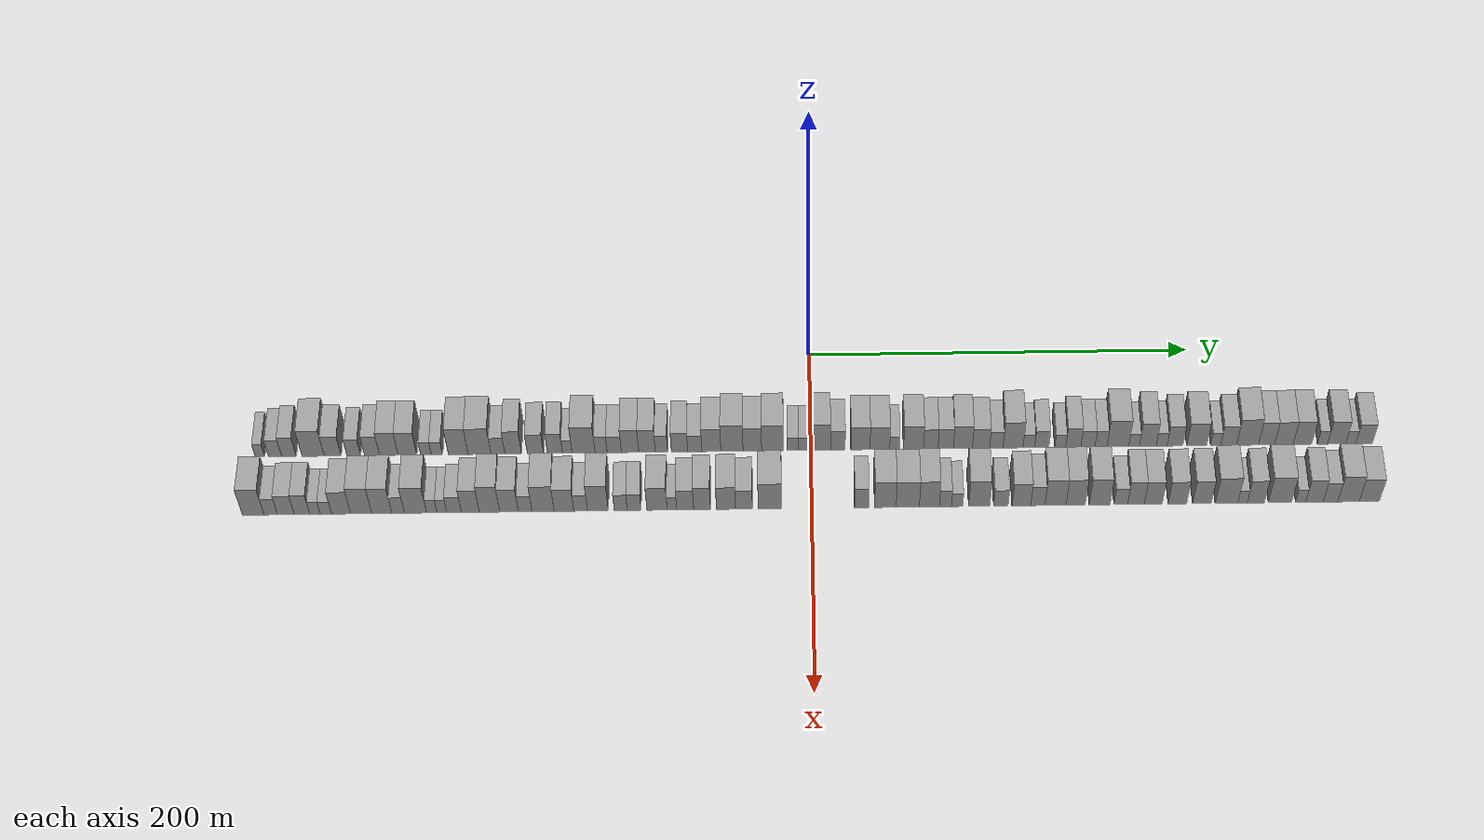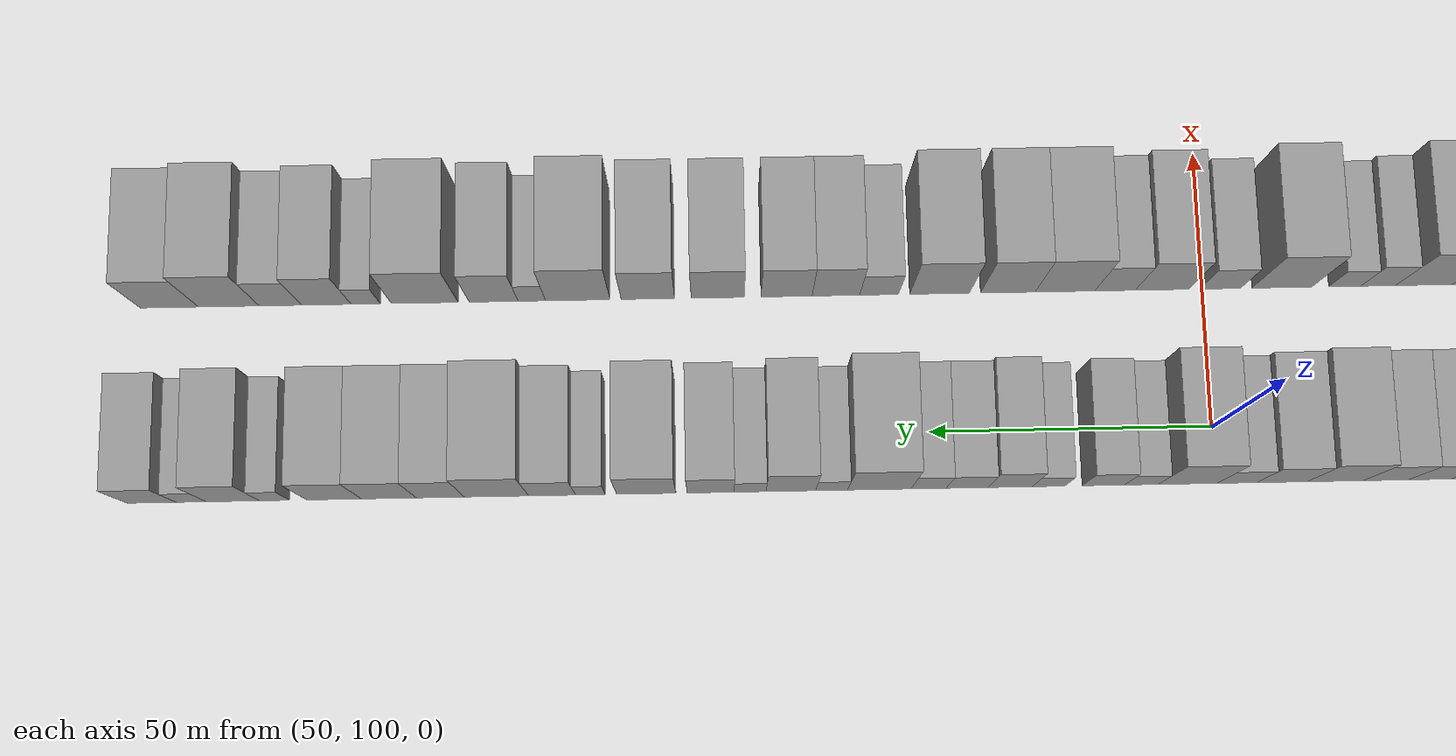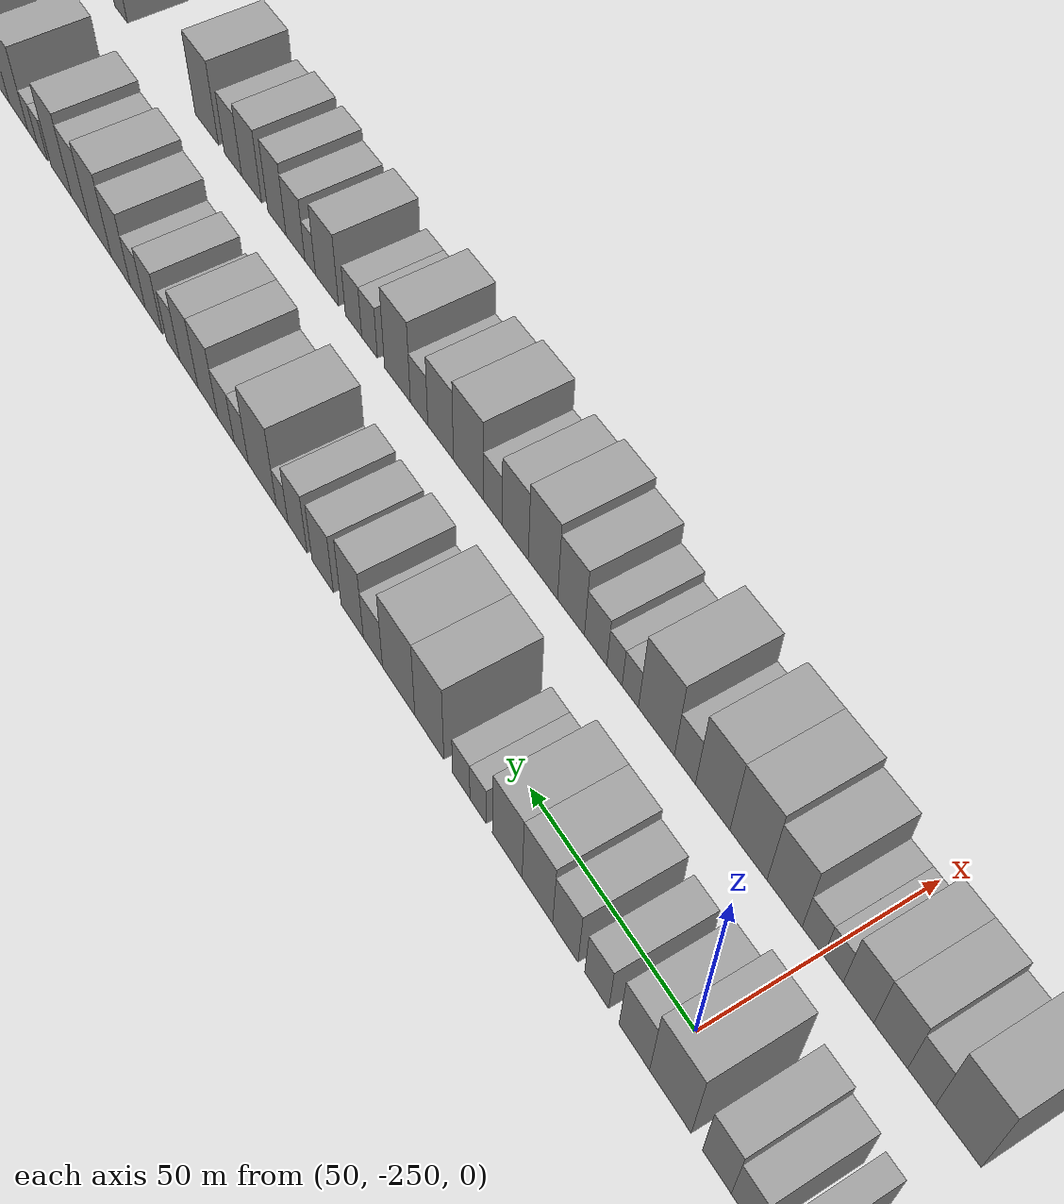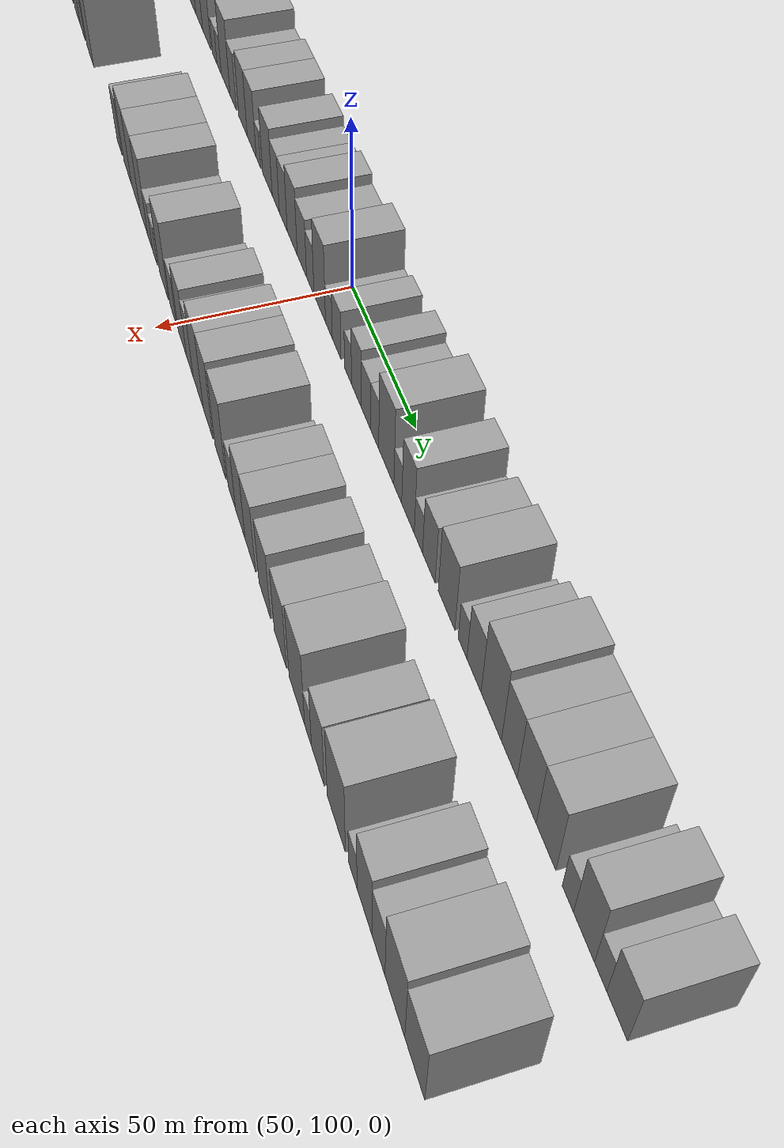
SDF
<sdf version="1.6">
 <world name="default">
  <scene>
   <sky><clouds><speed>12</speed></clouds></sky>
   <ambient>0.4 0.4 0.4 1</ambient>
   <background>0.7 0.7 0.7 1</background>
   <shadows>1</shadows>
  </scene>
  <gravity>0 0 -9.8066</gravity>
  <magnetic_field>6e-06 2.3e-05 -4.2e-05</magnetic_field>
  <physics default="0" name="default_physics" type="ode">
   <ode>
    <solver>
     <type>quick</type>
     <iters>10</iters>
     <sor>1.0</sor>
     <use_dynamic_moi_rescaling>0</use_dynamic_moi_rescaling>
    </solver>
    <constraints>
     <cfm>0</cfm>
     <erp>0.2</erp>
     <contact_max_correcting_vel>100</contact_max_correcting_vel>
     <contact_surface_layer>0.001</contact_surface_layer>
    </constraints>
   </ode>
   <max_step_size>0.004</max_step_size>
   <real_time_factor>1</real_time_factor>
   <real_time_update_rate>250</real_time_update_rate>
  </physics>
  <light name="sun" type="directional">
   <pose>0 0 10 0 0 0</pose>
   <diffuse>0.8 0.8 0.8 1</diffuse>
   <specular>0.2 0.2 0.2 1</specular>
   <attenuation>
    <range>1000</range>
    <constant>0.9</constant>
    <linear>0.01</linear>
    <quadratic>0.001</quadratic>
   </attenuation>
   <direction>-0.5 0.1 -0.9</direction>
  </light>
  <model name="building_1">
   <static>1</static>
   <pose>50.0000 -284.5821 0 0.000000 0.000000 0.000000</pose>
   <link name="link">
    <pose>0 0 6.00 0 0 0</pose>
    <collision name="collision"><geometry><box><size>20.0000 4.8358 12.0000</size></box></geometry></collision>
    <visual name="visual">
     <cast_shadows>0</cast_shadows>
     <geometry><box><size>20.0000 4.8358 12.0000</size></box></geometry>
     <material>
      <script>
       <uri>model://grey_wall/materials/scripts</uri>
       <uri>model://grey_wall/materials/textures</uri>
       <name>vrc/grey_wall</name>
      </script>
     </material>
    </visual>
   </link>
  </model>
  <model name="building_2">
   <static>1</static>
   <pose>50.0000 -276.7835 0 0.000000 0.000000 0.000000</pose>
   <link name="link">
    <pose>0 0 7.50 0 0 0</pose>
    <collision name="collision"><geometry><box><size>20.0000 6.7614 15.0000</size></box></geometry></collision>
    <visual name="visual">
     <cast_shadows>0</cast_shadows>
     <geometry><box><size>20.0000 6.7614 15.0000</size></box></geometry>
     <material>
      <script>
       <uri>model://grey_wall/materials/scripts</uri>
       <uri>model://grey_wall/materials/textures</uri>
       <name>vrc/grey_wall</name>
      </script>
     </material>
    </visual>
   </link>
  </model>
  <model name="building_3">
   <static>1</static>
   <pose>50.0000 -269.6287 0 0.000000 0.000000 0.000000</pose>
   <link name="link">
    <pose>0 0 9.00 0 0 0</pose>
    <collision name="collision"><geometry><box><size>20.0000 7.5483 18.0000</size></box></geometry></collision>
    <visual name="visual">
     <cast_shadows>0</cast_shadows>
     <geometry><box><size>20.0000 7.5483 18.0000</size></box></geometry>
     <material>
      <script>
       <uri>model://grey_wall/materials/scripts</uri>
       <uri>model://grey_wall/materials/textures</uri>
       <name>vrc/grey_wall</name>
      </script>
     </material>
    </visual>
   </link>
  </model>
  <model name="building_4">
   <static>1</static>
   <pose>50.0000 -257.1245 0 0.000000 0.000000 0.000000</pose>
   <link name="link">
    <pose>0 0 12.00 0 0 0</pose>
    <collision name="collision"><geometry><box><size>20.0000 11.4601 24.0000</size></box></geometry></collision>
    <visual name="visual">
     <cast_shadows>0</cast_shadows>
     <geometry><box><size>20.0000 11.4601 24.0000</size></box></geometry>
     <material>
      <script>
       <uri>model://grey_wall/materials/scripts</uri>
       <uri>model://grey_wall/materials/textures</uri>
       <name>vrc/grey_wall</name>
      </script>
     </material>
    </visual>
   </link>
  </model>
  <model name="building_5">
   <static>1</static>
   <pose>50.0000 -247.0553 0 0.000000 0.000000 0.000000</pose>
   <link name="link">
    <pose>0 0 9.00 0 0 0</pose>
    <collision name="collision"><geometry><box><size>20.0000 8.6783 18.0000</size></box></geometry></collision>
    <visual name="visual">
     <cast_shadows>0</cast_shadows>
     <geometry><box><size>20.0000 8.6783 18.0000</size></box></geometry>
     <material>
      <script>
       <uri>model://grey_wall/materials/scripts</uri>
       <uri>model://grey_wall/materials/textures</uri>
       <name>vrc/grey_wall</name>
      </script>
     </material>
    </visual>
   </link>
  </model>
  <model name="building_6">
   <static>1</static>
   <pose>50.0000 -236.1690 0 0.000000 0.000000 0.000000</pose>
   <link name="link">
    <pose>0 0 7.50 0 0 0</pose>
    <collision name="collision"><geometry><box><size>20.0000 7.0943 15.0000</size></box></geometry></collision>
    <visual name="visual">
     <cast_shadows>0</cast_shadows>
     <geometry><box><size>20.0000 7.0943 15.0000</size></box></geometry>
     <material>
      <script>
       <uri>model://grey_wall/materials/scripts</uri>
       <uri>model://grey_wall/materials/textures</uri>
       <name>vrc/grey_wall</name>
      </script>
     </material>
    </visual>
   </link>
  </model>
  <model name="building_7">
   <static>1</static>
   <pose>50.0000 -226.7389 0 0.000000 0.000000 0.000000</pose>
   <link name="link">
    <pose>0 0 9.00 0 0 0</pose>
    <collision name="collision"><geometry><box><size>20.0000 7.7658 18.0000</size></box></geometry></collision>
    <visual name="visual">
     <cast_shadows>0</cast_shadows>
     <geometry><box><size>20.0000 7.7658 18.0000</size></box></geometry>
     <material>
      <script>
       <uri>model://grey_wall/materials/scripts</uri>
       <uri>model://grey_wall/materials/textures</uri>
       <name>vrc/grey_wall</name>
      </script>
     </material>
    </visual>
   </link>
  </model>
  <model name="building_8">
   <static>1</static>
   <pose>50.0000 -218.0678 0 0.000000 0.000000 0.000000</pose>
   <link name="link">
    <pose>0 0 10.50 0 0 0</pose>
    <collision name="collision"><geometry><box><size>20.0000 9.5763 21.0000</size></box></geometry></collision>
    <visual name="visual">
     <cast_shadows>0</cast_shadows>
     <geometry><box><size>20.0000 9.5763 21.0000</size></box></geometry>
     <material>
      <script>
       <uri>model://grey_wall/materials/scripts</uri>
       <uri>model://grey_wall/materials/textures</uri>
       <name>vrc/grey_wall</name>
      </script>
     </material>
    </visual>
   </link>
  </model>
  <model name="building_9">
   <static>1</static>
   <pose>50.0000 -208.4706 0 0.000000 0.000000 0.000000</pose>
   <link name="link">
    <pose>0 0 10.50 0 0 0</pose>
    <collision name="collision"><geometry><box><size>20.0000 9.6182 21.0000</size></box></geometry></collision>
    <visual name="visual">
     <cast_shadows>0</cast_shadows>
     <geometry><box><size>20.0000 9.6182 21.0000</size></box></geometry>
     <material>
      <script>
       <uri>model://grey_wall/materials/scripts</uri>
       <uri>model://grey_wall/materials/textures</uri>
       <name>vrc/grey_wall</name>
      </script>
     </material>
    </visual>
   </link>
  </model>
  <model name="building_10">
   <static>1</static>
   <pose>50.0000 -198.9174 0 0.000000 0.000000 0.000000</pose>
   <link name="link">
    <pose>0 0 6.00 0 0 0</pose>
    <collision name="collision"><geometry><box><size>20.0000 5.4881 12.0000</size></box></geometry></collision>
    <visual name="visual">
     <cast_shadows>0</cast_shadows>
     <geometry><box><size>20.0000 5.4881 12.0000</size></box></geometry>
     <material>
      <script>
       <uri>model://grey_wall/materials/scripts</uri>
       <uri>model://grey_wall/materials/textures</uri>
       <name>vrc/grey_wall</name>
      </script>
     </material>
    </visual>
   </link>
  </model>
  <model name="building_11">
   <static>1</static>
   <pose>50.0000 -193.2363 0 0.000000 0.000000 0.000000</pose>
   <link name="link">
    <pose>0 0 6.00 0 0 0</pose>
    <collision name="collision"><geometry><box><size>20.0000 5.8742 12.0000</size></box></geometry></collision>
    <visual name="visual">
     <cast_shadows>0</cast_shadows>
     <geometry><box><size>20.0000 5.8742 12.0000</size></box></geometry>
     <material>
      <script>
       <uri>model://grey_wall/materials/scripts</uri>
       <uri>model://grey_wall/materials/textures</uri>
       <name>vrc/grey_wall</name>
      </script>
     </material>
    </visual>
   </link>
  </model>
  <model name="building_12">
   <static>1</static>
   <pose>50.0000 -182.2028 0 0.000000 0.000000 0.000000</pose>
   <link name="link">
    <pose>0 0 12.00 0 0 0</pose>
    <collision name="collision"><geometry><box><size>20.0000 10.1927 24.0000</size></box></geometry></collision>
    <visual name="visual">
     <cast_shadows>0</cast_shadows>
     <geometry><box><size>20.0000 10.1927 24.0000</size></box></geometry>
     <material>
      <script>
       <uri>model://grey_wall/materials/scripts</uri>
       <uri>model://grey_wall/materials/textures</uri>
       <name>vrc/grey_wall</name>
      </script>
     </material>
    </visual>
   </link>
  </model>
  <model name="building_13">
   <static>1</static>
   <pose>50.0000 -171.2083 0 0.000000 0.000000 0.000000</pose>
   <link name="link">
    <pose>0 0 12.00 0 0 0</pose>
    <collision name="collision"><geometry><box><size>20.0000 11.7963 24.0000</size></box></geometry></collision>
    <visual name="visual">
     <cast_shadows>0</cast_shadows>
     <geometry><box><size>20.0000 11.7963 24.0000</size></box></geometry>
     <material>
      <script>
       <uri>model://grey_wall/materials/scripts</uri>
       <uri>model://grey_wall/materials/textures</uri>
       <name>vrc/grey_wall</name>
      </script>
     </material>
    </visual>
   </link>
  </model>
  <model name="building_14">
   <static>1</static>
   <pose>50.0000 -161.7146 0 0.000000 0.000000 0.000000</pose>
   <link name="link">
    <pose>0 0 7.50 0 0 0</pose>
    <collision name="collision"><geometry><box><size>20.0000 7.1911 15.0000</size></box></geometry></collision>
    <visual name="visual">
     <cast_shadows>0</cast_shadows>
     <geometry><box><size>20.0000 7.1911 15.0000</size></box></geometry>
     <material>
      <script>
       <uri>model://grey_wall/materials/scripts</uri>
       <uri>model://grey_wall/materials/textures</uri>
       <name>vrc/grey_wall</name>
      </script>
     </material>
    </visual>
   </link>
  </model>
  <model name="building_15">
   <static>1</static>
   <pose>50.0000 -153.8216 0 0.000000 0.000000 0.000000</pose>
   <link name="link">
    <pose>0 0 10.50 0 0 0</pose>
    <collision name="collision"><geometry><box><size>20.0000 8.5948 21.0000</size></box></geometry></collision>
    <visual name="visual">
     <cast_shadows>0</cast_shadows>
     <geometry><box><size>20.0000 8.5948 21.0000</size></box></geometry>
     <material>
      <script>
       <uri>model://grey_wall/materials/scripts</uri>
       <uri>model://grey_wall/materials/textures</uri>
       <name>vrc/grey_wall</name>
      </script>
     </material>
    </visual>
   </link>
  </model>
  <model name="building_16">
   <static>1</static>
   <pose>50.0000 -142.3034 0 0.000000 0.000000 0.000000</pose>
   <link name="link">
    <pose>0 0 9.00 0 0 0</pose>
    <collision name="collision"><geometry><box><size>20.0000 8.4416 18.0000</size></box></geometry></collision>
    <visual name="visual">
     <cast_shadows>0</cast_shadows>
     <geometry><box><size>20.0000 8.4416 18.0000</size></box></geometry>
     <material>
      <script>
       <uri>model://grey_wall/materials/scripts</uri>
       <uri>model://grey_wall/materials/textures</uri>
       <name>vrc/grey_wall</name>
      </script>
     </material>
    </visual>
   </link>
  </model>
  <model name="building_17">
   <static>1</static>
   <pose>50.0000 -132.2078 0 0.000000 0.000000 0.000000</pose>
   <link name="link">
    <pose>0 0 9.00 0 0 0</pose>
    <collision name="collision"><geometry><box><size>20.0000 7.7498 18.0000</size></box></geometry></collision>
    <visual name="visual">
     <cast_shadows>0</cast_shadows>
     <geometry><box><size>20.0000 7.7498 18.0000</size></box></geometry>
     <material>
      <script>
       <uri>model://grey_wall/materials/scripts</uri>
       <uri>model://grey_wall/materials/textures</uri>
       <name>vrc/grey_wall</name>
      </script>
     </material>
    </visual>
   </link>
  </model>
  <model name="building_18">
   <static>1</static>
   <pose>50.0000 -125.8499 0 0.000000 0.000000 0.000000</pose>
   <link name="link">
    <pose>0 0 6.00 0 0 0</pose>
    <collision name="collision"><geometry><box><size>20.0000 4.9659 12.0000</size></box></geometry></collision>
    <visual name="visual">
     <cast_shadows>0</cast_shadows>
     <geometry><box><size>20.0000 4.9659 12.0000</size></box></geometry>
     <material>
      <script>
       <uri>model://grey_wall/materials/scripts</uri>
       <uri>model://grey_wall/materials/textures</uri>
       <name>vrc/grey_wall</name>
      </script>
     </material>
    </visual>
   </link>
  </model>
  <model name="building_19">
   <static>1</static>
   <pose>50.0000 -117.4354 0 0.000000 0.000000 0.000000</pose>
   <link name="link">
    <pose>0 0 12.00 0 0 0</pose>
    <collision name="collision"><geometry><box><size>20.0000 11.8631 24.0000</size></box></geometry></collision>
    <visual name="visual">
     <cast_shadows>0</cast_shadows>
     <geometry><box><size>20.0000 11.8631 24.0000</size></box></geometry>
     <material>
      <script>
       <uri>model://grey_wall/materials/scripts</uri>
       <uri>model://grey_wall/materials/textures</uri>
       <name>vrc/grey_wall</name>
      </script>
     </material>
    </visual>
   </link>
  </model>
  <model name="building_20">
   <static>1</static>
   <pose>50.0000 -108.3577 0 0.000000 0.000000 0.000000</pose>
   <link name="link">
    <pose>0 0 7.50 0 0 0</pose>
    <collision name="collision"><geometry><box><size>20.0000 6.2923 15.0000</size></box></geometry></collision>
    <visual name="visual">
     <cast_shadows>0</cast_shadows>
     <geometry><box><size>20.0000 6.2923 15.0000</size></box></geometry>
     <material>
      <script>
       <uri>model://grey_wall/materials/scripts</uri>
       <uri>model://grey_wall/materials/textures</uri>
       <name>vrc/grey_wall</name>
      </script>
     </material>
    </visual>
   </link>
  </model>
  <model name="building_21">
   <static>1</static>
   <pose>50.0000 -101.5367 0 0.000000 0.000000 0.000000</pose>
   <link name="link">
    <pose>0 0 7.50 0 0 0</pose>
    <collision name="collision"><geometry><box><size>20.0000 7.3498 15.0000</size></box></geometry></collision>
    <visual name="visual">
     <cast_shadows>0</cast_shadows>
     <geometry><box><size>20.0000 7.3498 15.0000</size></box></geometry>
     <material>
      <script>
       <uri>model://grey_wall/materials/scripts</uri>
       <uri>model://grey_wall/materials/textures</uri>
       <name>vrc/grey_wall</name>
      </script>
     </material>
    </visual>
   </link>
  </model>
  <model name="building_22">
   <static>1</static>
   <pose>50.0000 -93.3873 0 0.000000 0.000000 0.000000</pose>
   <link name="link">
    <pose>0 0 10.50 0 0 0</pose>
    <collision name="collision"><geometry><box><size>20.0000 8.9489 21.0000</size></box></geometry></collision>
    <visual name="visual">
     <cast_shadows>0</cast_shadows>
     <geometry><box><size>20.0000 8.9489 21.0000</size></box></geometry>
     <material>
      <script>
       <uri>model://grey_wall/materials/scripts</uri>
       <uri>model://grey_wall/materials/textures</uri>
       <name>vrc/grey_wall</name>
      </script>
     </material>
    </visual>
   </link>
  </model>
  <model name="building_23">
   <static>1</static>
   <pose>50.0000 -84.6043 0 0.000000 0.000000 0.000000</pose>
   <link name="link">
    <pose>0 0 10.50 0 0 0</pose>
    <collision name="collision"><geometry><box><size>20.0000 8.6171 21.0000</size></box></geometry></collision>
    <visual name="visual">
     <cast_shadows>0</cast_shadows>
     <geometry><box><size>20.0000 8.6171 21.0000</size></box></geometry>
     <material>
      <script>
       <uri>model://grey_wall/materials/scripts</uri>
       <uri>model://grey_wall/materials/textures</uri>
       <name>vrc/grey_wall</name>
      </script>
     </material>
    </visual>
   </link>
  </model>
  <model name="building_24">
   <static>1</static>
   <pose>50.0000 -77.1314 0 0.000000 0.000000 0.000000</pose>
   <link name="link">
    <pose>0 0 7.50 0 0 0</pose>
    <collision name="collision"><geometry><box><size>20.0000 6.3286 15.0000</size></box></geometry></collision>
    <visual name="visual">
     <cast_shadows>0</cast_shadows>
     <geometry><box><size>20.0000 6.3286 15.0000</size></box></geometry>
     <material>
      <script>
       <uri>model://grey_wall/materials/scripts</uri>
       <uri>model://grey_wall/materials/textures</uri>
       <name>vrc/grey_wall</name>
      </script>
     </material>
    </visual>
   </link>
  </model>
  <model name="building_25">
   <static>1</static>
   <pose>50.0000 -67.7709 0 0.000000 0.000000 0.000000</pose>
   <link name="link">
    <pose>0 0 9.00 0 0 0</pose>
    <collision name="collision"><geometry><box><size>20.0000 8.3924 18.0000</size></box></geometry></collision>
    <visual name="visual">
     <cast_shadows>0</cast_shadows>
     <geometry><box><size>20.0000 8.3924 18.0000</size></box></geometry>
     <material>
      <script>
       <uri>model://grey_wall/materials/scripts</uri>
       <uri>model://grey_wall/materials/textures</uri>
       <name>vrc/grey_wall</name>
      </script>
     </material>
    </visual>
   </link>
  </model>
  <model name="building_26">
   <static>1</static>
   <pose>50.0000 -59.8988 0 0.000000 0.000000 0.000000</pose>
   <link name="link">
    <pose>0 0 7.50 0 0 0</pose>
    <collision name="collision"><geometry><box><size>20.0000 7.3519 15.0000</size></box></geometry></collision>
    <visual name="visual">
     <cast_shadows>0</cast_shadows>
     <geometry><box><size>20.0000 7.3519 15.0000</size></box></geometry>
     <material>
      <script>
       <uri>model://grey_wall/materials/scripts</uri>
       <uri>model://grey_wall/materials/textures</uri>
       <name>vrc/grey_wall</name>
      </script>
     </material>
    </visual>
   </link>
  </model>
  <model name="building_27">
   <static>1</static>
   <pose>50.0000 -51.3166 0 0.000000 0.000000 0.000000</pose>
   <link name="link">
    <pose>0 0 10.50 0 0 0</pose>
    <collision name="collision"><geometry><box><size>20.0000 9.8125 21.0000</size></box></geometry></collision>
    <visual name="visual">
     <cast_shadows>0</cast_shadows>
     <geometry><box><size>20.0000 9.8125 21.0000</size></box></geometry>
     <material>
      <script>
       <uri>model://grey_wall/materials/scripts</uri>
       <uri>model://grey_wall/materials/textures</uri>
       <name>vrc/grey_wall</name>
      </script>
     </material>
    </visual>
   </link>
  </model>
  <model name="building_28">
   <static>1</static>
   <pose>50.0000 -40.6690 0 0.000000 0.000000 0.000000</pose>
   <link name="link">
    <pose>0 0 12.00 0 0 0</pose>
    <collision name="collision"><geometry><box><size>20.0000 11.4826 24.0000</size></box></geometry></collision>
    <visual name="visual">
     <cast_shadows>0</cast_shadows>
     <geometry><box><size>20.0000 11.4826 24.0000</size></box></geometry>
     <material>
      <script>
       <uri>model://grey_wall/materials/scripts</uri>
       <uri>model://grey_wall/materials/textures</uri>
       <name>vrc/grey_wall</name>
      </script>
     </material>
    </visual>
   </link>
  </model>
  <model name="building_29">
   <static>1</static>
   <pose>50.0000 -30.1226 0 0.000000 0.000000 0.000000</pose>
   <link name="link">
    <pose>0 0 10.50 0 0 0</pose>
    <collision name="collision"><geometry><box><size>20.0000 9.6104 21.0000</size></box></geometry></collision>
    <visual name="visual">
     <cast_shadows>0</cast_shadows>
     <geometry><box><size>20.0000 9.6104 21.0000</size></box></geometry>
     <material>
      <script>
       <uri>model://grey_wall/materials/scripts</uri>
       <uri>model://grey_wall/materials/textures</uri>
       <name>vrc/grey_wall</name>
      </script>
     </material>
    </visual>
   </link>
  </model>
  <model name="building_30">
   <static>1</static>
   <pose>50.0000 -19.6471 0 0.000000 0.000000 0.000000</pose>
   <link name="link">
    <pose>0 0 12.00 0 0 0</pose>
    <collision name="collision"><geometry><box><size>20.0000 11.3405 24.0000</size></box></geometry></collision>
    <visual name="visual">
     <cast_shadows>0</cast_shadows>
     <geometry><box><size>20.0000 11.3405 24.0000</size></box></geometry>
     <material>
      <script>
       <uri>model://grey_wall/materials/scripts</uri>
       <uri>model://grey_wall/materials/textures</uri>
       <name>vrc/grey_wall</name>
      </script>
     </material>
    </visual>
   </link>
  </model>
  <model name="building_31">
   <static>1</static>
   <pose>50.0000 -9.0695 0 0.000000 0.000000 0.000000</pose>
   <link name="link">
    <pose>0 0 6.00 0 0 0</pose>
    <collision name="collision"><geometry><box><size>20.0000 5.8147 12.0000</size></box></geometry></collision>
    <visual name="visual">
     <cast_shadows>0</cast_shadows>
     <geometry><box><size>20.0000 5.8147 12.0000</size></box></geometry>
     <material>
      <script>
       <uri>model://grey_wall/materials/scripts</uri>
       <uri>model://grey_wall/materials/textures</uri>
       <name>vrc/grey_wall</name>
      </script>
     </material>
    </visual>
   </link>
  </model>
  <model name="building_32">
   <static>1</static>
   <pose>50.0000 -3.4309 0 0.000000 0.000000 0.000000</pose>
   <link name="link">
    <pose>0 0 6.00 0 0 0</pose>
    <collision name="collision"><geometry><box><size>20.0000 5.4626 12.0000</size></box></geometry></collision>
    <visual name="visual">
     <cast_shadows>0</cast_shadows>
     <geometry><box><size>20.0000 5.4626 12.0000</size></box></geometry>
     <material>
      <script>
       <uri>model://grey_wall/materials/scripts</uri>
       <uri>model://grey_wall/materials/textures</uri>
       <name>vrc/grey_wall</name>
      </script>
     </material>
    </visual>
   </link>
  </model>
  <model name="building_33">
   <static>1</static>
   <pose>50.0000 4.8221 0 0.000000 0.000000 0.000000</pose>
   <link name="link">
    <pose>0 0 12.00 0 0 0</pose>
    <collision name="collision"><geometry><box><size>20.0000 11.0434 24.0000</size></box></geometry></collision>
    <visual name="visual">
     <cast_shadows>0</cast_shadows>
     <geometry><box><size>20.0000 11.0434 24.0000</size></box></geometry>
     <material>
      <script>
       <uri>model://grey_wall/materials/scripts</uri>
       <uri>model://grey_wall/materials/textures</uri>
       <name>vrc/grey_wall</name>
      </script>
     </material>
    </visual>
   </link>
  </model>
  <model name="building_34">
   <static>1</static>
   <pose>50.0000 14.1204 0 0.000000 0.000000 0.000000</pose>
   <link name="link">
    <pose>0 0 9.00 0 0 0</pose>
    <collision name="collision"><geometry><box><size>20.0000 7.5531 18.0000</size></box></geometry></collision>
    <visual name="visual">
     <cast_shadows>0</cast_shadows>
     <geometry><box><size>20.0000 7.5531 18.0000</size></box></geometry>
     <material>
      <script>
       <uri>model://grey_wall/materials/scripts</uri>
       <uri>model://grey_wall/materials/textures</uri>
       <name>vrc/grey_wall</name>
      </script>
     </material>
    </visual>
   </link>
  </model>
  <model name="building_35">
   <static>1</static>
   <pose>50.0000 25.8246 0 0.000000 0.000000 0.000000</pose>
   <link name="link">
    <pose>0 0 10.50 0 0 0</pose>
    <collision name="collision"><geometry><box><size>20.0000 9.8552 21.0000</size></box></geometry></collision>
    <visual name="visual">
     <cast_shadows>0</cast_shadows>
     <geometry><box><size>20.0000 9.8552 21.0000</size></box></geometry>
     <material>
      <script>
       <uri>model://grey_wall/materials/scripts</uri>
       <uri>model://grey_wall/materials/textures</uri>
       <name>vrc/grey_wall</name>
      </script>
     </material>
    </visual>
   </link>
  </model>
  <model name="building_36">
   <static>1</static>
   <pose>50.0000 35.8675 0 0.000000 0.000000 0.000000</pose>
   <link name="link">
    <pose>0 0 10.50 0 0 0</pose>
    <collision name="collision"><geometry><box><size>20.0000 10.2308 21.0000</size></box></geometry></collision>
    <visual name="visual">
     <cast_shadows>0</cast_shadows>
     <geometry><box><size>20.0000 10.2308 21.0000</size></box></geometry>
     <material>
      <script>
       <uri>model://grey_wall/materials/scripts</uri>
       <uri>model://grey_wall/materials/textures</uri>
       <name>vrc/grey_wall</name>
      </script>
     </material>
    </visual>
   </link>
  </model>
  <model name="building_37">
   <static>1</static>
   <pose>50.0000 43.5499 0 0.000000 0.000000 0.000000</pose>
   <link name="link">
    <pose>0 0 6.00 0 0 0</pose>
    <collision name="collision"><geometry><box><size>20.0000 5.1339 12.0000</size></box></geometry></collision>
    <visual name="visual">
     <cast_shadows>0</cast_shadows>
     <geometry><box><size>20.0000 5.1339 12.0000</size></box></geometry>
     <material>
      <script>
       <uri>model://grey_wall/materials/scripts</uri>
       <uri>model://grey_wall/materials/textures</uri>
       <name>vrc/grey_wall</name>
      </script>
     </material>
    </visual>
   </link>
  </model>
  <model name="building_38">
   <static>1</static>
   <pose>50.0000 53.2975 0 0.000000 0.000000 0.000000</pose>
   <link name="link">
    <pose>0 0 10.50 0 0 0</pose>
    <collision name="collision"><geometry><box><size>20.0000 10.3613 21.0000</size></box></geometry></collision>
    <visual name="visual">
     <cast_shadows>0</cast_shadows>
     <geometry><box><size>20.0000 10.3613 21.0000</size></box></geometry>
     <material>
      <script>
       <uri>model://grey_wall/materials/scripts</uri>
       <uri>model://grey_wall/materials/textures</uri>
       <name>vrc/grey_wall</name>
      </script>
     </material>
    </visual>
   </link>
  </model>
  <model name="building_39">
   <static>1</static>
   <pose>50.0000 62.2341 0 0.000000 0.000000 0.000000</pose>
   <link name="link">
    <pose>0 0 9.00 0 0 0</pose>
    <collision name="collision"><geometry><box><size>20.0000 7.5119 18.0000</size></box></geometry></collision>
    <visual name="visual">
     <cast_shadows>0</cast_shadows>
     <geometry><box><size>20.0000 7.5119 18.0000</size></box></geometry>
     <material>
      <script>
       <uri>model://grey_wall/materials/scripts</uri>
       <uri>model://grey_wall/materials/textures</uri>
       <name>vrc/grey_wall</name>
      </script>
     </material>
    </visual>
   </link>
  </model>
  <model name="building_40">
   <static>1</static>
   <pose>50.0000 69.9717 0 0.000000 0.000000 0.000000</pose>
   <link name="link">
    <pose>0 0 9.00 0 0 0</pose>
    <collision name="collision"><geometry><box><size>20.0000 7.9632 18.0000</size></box></geometry></collision>
    <visual name="visual">
     <cast_shadows>0</cast_shadows>
     <geometry><box><size>20.0000 7.9632 18.0000</size></box></geometry>
     <material>
      <script>
       <uri>model://grey_wall/materials/scripts</uri>
       <uri>model://grey_wall/materials/textures</uri>
       <name>vrc/grey_wall</name>
      </script>
     </material>
    </visual>
   </link>
  </model>
  <model name="building_41">
   <static>1</static>
   <pose>50.0000 78.8873 0 0.000000 0.000000 0.000000</pose>
   <link name="link">
    <pose>0 0 10.50 0 0 0</pose>
    <collision name="collision"><geometry><box><size>20.0000 9.8679 21.0000</size></box></geometry></collision>
    <visual name="visual">
     <cast_shadows>0</cast_shadows>
     <geometry><box><size>20.0000 9.8679 21.0000</size></box></geometry>
     <material>
      <script>
       <uri>model://grey_wall/materials/scripts</uri>
       <uri>model://grey_wall/materials/textures</uri>
       <name>vrc/grey_wall</name>
      </script>
     </material>
    </visual>
   </link>
  </model>
  <model name="building_42">
   <static>1</static>
   <pose>50.0000 88.2844 0 0.000000 0.000000 0.000000</pose>
   <link name="link">
    <pose>0 0 9.00 0 0 0</pose>
    <collision name="collision"><geometry><box><size>20.0000 8.9264 18.0000</size></box></geometry></collision>
    <visual name="visual">
     <cast_shadows>0</cast_shadows>
     <geometry><box><size>20.0000 8.9264 18.0000</size></box></geometry>
     <material>
      <script>
       <uri>model://grey_wall/materials/scripts</uri>
       <uri>model://grey_wall/materials/textures</uri>
       <name>vrc/grey_wall</name>
      </script>
     </material>
    </visual>
   </link>
  </model>
  <model name="building_43">
   <static>1</static>
   <pose>50.0000 96.2258 0 0.000000 0.000000 0.000000</pose>
   <link name="link">
    <pose>0 0 7.50 0 0 0</pose>
    <collision name="collision"><geometry><box><size>20.0000 6.9563 15.0000</size></box></geometry></collision>
    <visual name="visual">
     <cast_shadows>0</cast_shadows>
     <geometry><box><size>20.0000 6.9563 15.0000</size></box></geometry>
     <material>
      <script>
       <uri>model://grey_wall/materials/scripts</uri>
       <uri>model://grey_wall/materials/textures</uri>
       <name>vrc/grey_wall</name>
      </script>
     </material>
    </visual>
   </link>
  </model>
  <model name="building_44">
   <static>1</static>
   <pose>50.0000 104.8939 0 0.000000 0.000000 0.000000</pose>
   <link name="link">
    <pose>0 0 12.00 0 0 0</pose>
    <collision name="collision"><geometry><box><size>20.0000 10.3800 24.0000</size></box></geometry></collision>
    <visual name="visual">
     <cast_shadows>0</cast_shadows>
     <geometry><box><size>20.0000 10.3800 24.0000</size></box></geometry>
     <material>
      <script>
       <uri>model://grey_wall/materials/scripts</uri>
       <uri>model://grey_wall/materials/textures</uri>
       <name>vrc/grey_wall</name>
      </script>
     </material>
    </visual>
   </link>
  </model>
  <model name="building_45">
   <static>1</static>
   <pose>50.0000 113.0699 0 0.000000 0.000000 0.000000</pose>
   <link name="link">
    <pose>0 0 6.00 0 0 0</pose>
    <collision name="collision"><geometry><box><size>20.0000 5.9718 12.0000</size></box></geometry></collision>
    <visual name="visual">
     <cast_shadows>0</cast_shadows>
     <geometry><box><size>20.0000 5.9718 12.0000</size></box></geometry>
     <material>
      <script>
       <uri>model://grey_wall/materials/scripts</uri>
       <uri>model://grey_wall/materials/textures</uri>
       <name>vrc/grey_wall</name>
      </script>
     </material>
    </visual>
   </link>
  </model>
  <model name="building_46">
   <static>1</static>
   <pose>50.0000 119.7701 0 0.000000 0.000000 0.000000</pose>
   <link name="link">
    <pose>0 0 7.50 0 0 0</pose>
    <collision name="collision"><geometry><box><size>20.0000 7.4286 15.0000</size></box></geometry></collision>
    <visual name="visual">
     <cast_shadows>0</cast_shadows>
     <geometry><box><size>20.0000 7.4286 15.0000</size></box></geometry>
     <material>
      <script>
       <uri>model://grey_wall/materials/scripts</uri>
       <uri>model://grey_wall/materials/textures</uri>
       <name>vrc/grey_wall</name>
      </script>
     </material>
    </visual>
   </link>
  </model>
  <model name="building_47">
   <static>1</static>
   <pose>50.0000 129.3708 0 0.000000 0.000000 0.000000</pose>
   <link name="link">
    <pose>0 0 6.00 0 0 0</pose>
    <collision name="collision"><geometry><box><size>20.0000 5.7727 12.0000</size></box></geometry></collision>
    <visual name="visual">
     <cast_shadows>0</cast_shadows>
     <geometry><box><size>20.0000 5.7727 12.0000</size></box></geometry>
     <material>
      <script>
       <uri>model://grey_wall/materials/scripts</uri>
       <uri>model://grey_wall/materials/textures</uri>
       <name>vrc/grey_wall</name>
      </script>
     </material>
    </visual>
   </link>
  </model>
  <model name="building_48">
   <static>1</static>
   <pose>50.0000 136.1552 0 0.000000 0.000000 0.000000</pose>
   <link name="link">
    <pose>0 0 9.00 0 0 0</pose>
    <collision name="collision"><geometry><box><size>20.0000 7.7961 18.0000</size></box></geometry></collision>
    <visual name="visual">
     <cast_shadows>0</cast_shadows>
     <geometry><box><size>20.0000 7.7961 18.0000</size></box></geometry>
     <material>
      <script>
       <uri>model://grey_wall/materials/scripts</uri>
       <uri>model://grey_wall/materials/textures</uri>
       <name>vrc/grey_wall</name>
      </script>
     </material>
    </visual>
   </link>
  </model>
  <model name="building_49">
   <static>1</static>
   <pose>50.0000 143.7373 0 0.000000 0.000000 0.000000</pose>
   <link name="link">
    <pose>0 0 7.50 0 0 0</pose>
    <collision name="collision"><geometry><box><size>20.0000 7.3680 15.0000</size></box></geometry></collision>
    <visual name="visual">
     <cast_shadows>0</cast_shadows>
     <geometry><box><size>20.0000 7.3680 15.0000</size></box></geometry>
     <material>
      <script>
       <uri>model://grey_wall/materials/scripts</uri>
       <uri>model://grey_wall/materials/textures</uri>
       <name>vrc/grey_wall</name>
      </script>
     </material>
    </visual>
   </link>
  </model>
  <model name="building_50">
   <static>1</static>
   <pose>50.0000 150.5188 0 0.000000 0.000000 0.000000</pose>
   <link name="link">
    <pose>0 0 7.50 0 0 0</pose>
    <collision name="collision"><geometry><box><size>20.0000 6.1952 15.0000</size></box></geometry></collision>
    <visual name="visual">
     <cast_shadows>0</cast_shadows>
     <geometry><box><size>20.0000 6.1952 15.0000</size></box></geometry>
     <material>
      <script>
       <uri>model://grey_wall/materials/scripts</uri>
       <uri>model://grey_wall/materials/textures</uri>
       <name>vrc/grey_wall</name>
      </script>
     </material>
    </visual>
   </link>
  </model>
  <model name="building_51">
   <static>1</static>
   <pose>50.0000 159.2258 0 0.000000 0.000000 0.000000</pose>
   <link name="link">
    <pose>0 0 12.00 0 0 0</pose>
    <collision name="collision"><geometry><box><size>20.0000 11.2186 24.0000</size></box></geometry></collision>
    <visual name="visual">
     <cast_shadows>0</cast_shadows>
     <geometry><box><size>20.0000 11.2186 24.0000</size></box></geometry>
     <material>
      <script>
       <uri>model://grey_wall/materials/scripts</uri>
       <uri>model://grey_wall/materials/textures</uri>
       <name>vrc/grey_wall</name>
      </script>
     </material>
    </visual>
   </link>
  </model>
  <model name="building_52">
   <static>1</static>
   <pose>50.0000 167.6188 0 0.000000 0.000000 0.000000</pose>
   <link name="link">
    <pose>0 0 6.00 0 0 0</pose>
    <collision name="collision"><geometry><box><size>20.0000 5.5675 12.0000</size></box></geometry></collision>
    <visual name="visual">
     <cast_shadows>0</cast_shadows>
     <geometry><box><size>20.0000 5.5675 12.0000</size></box></geometry>
     <material>
      <script>
       <uri>model://grey_wall/materials/scripts</uri>
       <uri>model://grey_wall/materials/textures</uri>
       <name>vrc/grey_wall</name>
      </script>
     </material>
    </visual>
   </link>
  </model>
  <model name="building_53">
   <static>1</static>
   <pose>50.0000 174.7713 0 0.000000 0.000000 0.000000</pose>
   <link name="link">
    <pose>0 0 10.50 0 0 0</pose>
    <collision name="collision"><geometry><box><size>20.0000 8.7375 21.0000</size></box></geometry></collision>
    <visual name="visual">
     <cast_shadows>0</cast_shadows>
     <geometry><box><size>20.0000 8.7375 21.0000</size></box></geometry>
     <material>
      <script>
       <uri>model://grey_wall/materials/scripts</uri>
       <uri>model://grey_wall/materials/textures</uri>
       <name>vrc/grey_wall</name>
      </script>
     </material>
    </visual>
   </link>
  </model>
  <model name="building_54">
   <static>1</static>
   <pose>50.0000 181.9391 0 0.000000 0.000000 0.000000</pose>
   <link name="link">
    <pose>0 0 6.00 0 0 0</pose>
    <collision name="collision"><geometry><box><size>20.0000 5.5981 12.0000</size></box></geometry></collision>
    <visual name="visual">
     <cast_shadows>0</cast_shadows>
     <geometry><box><size>20.0000 5.5981 12.0000</size></box></geometry>
     <material>
      <script>
       <uri>model://grey_wall/materials/scripts</uri>
       <uri>model://grey_wall/materials/textures</uri>
       <name>vrc/grey_wall</name>
      </script>
     </material>
    </visual>
   </link>
  </model>
  <model name="building_55">
   <static>1</static>
   <pose>50.0000 188.8689 0 0.000000 0.000000 0.000000</pose>
   <link name="link">
    <pose>0 0 9.00 0 0 0</pose>
    <collision name="collision"><geometry><box><size>20.0000 8.2615 18.0000</size></box></geometry></collision>
    <visual name="visual">
     <cast_shadows>0</cast_shadows>
     <geometry><box><size>20.0000 8.2615 18.0000</size></box></geometry>
     <material>
      <script>
       <uri>model://grey_wall/materials/scripts</uri>
       <uri>model://grey_wall/materials/textures</uri>
       <name>vrc/grey_wall</name>
      </script>
     </material>
    </visual>
   </link>
  </model>
  <model name="building_56">
   <static>1</static>
   <pose>50.0000 200.1994 0 0.000000 0.000000 0.000000</pose>
   <link name="link">
    <pose>0 0 10.50 0 0 0</pose>
    <collision name="collision"><geometry><box><size>20.0000 10.3995 21.0000</size></box></geometry></collision>
    <visual name="visual">
     <cast_shadows>0</cast_shadows>
     <geometry><box><size>20.0000 10.3995 21.0000</size></box></geometry>
     <material>
      <script>
       <uri>model://grey_wall/materials/scripts</uri>
       <uri>model://grey_wall/materials/textures</uri>
       <name>vrc/grey_wall</name>
      </script>
     </material>
    </visual>
   </link>
  </model>
  <model name="building_57">
   <static>1</static>
   <pose>50.0000 210.0038 0 0.000000 0.000000 0.000000</pose>
   <link name="link">
    <pose>0 0 6.00 0 0 0</pose>
    <collision name="collision"><geometry><box><size>20.0000 5.2093 12.0000</size></box></geometry></collision>
    <visual name="visual">
     <cast_shadows>0</cast_shadows>
     <geometry><box><size>20.0000 5.2093 12.0000</size></box></geometry>
     <material>
      <script>
       <uri>model://grey_wall/materials/scripts</uri>
       <uri>model://grey_wall/materials/textures</uri>
       <name>vrc/grey_wall</name>
      </script>
     </material>
    </visual>
   </link>
  </model>
  <model name="building_58">
   <static>1</static>
   <pose>50.0000 216.7293 0 0.000000 0.000000 0.000000</pose>
   <link name="link">
    <pose>0 0 9.00 0 0 0</pose>
    <collision name="collision"><geometry><box><size>20.0000 8.2417 18.0000</size></box></geometry></collision>
    <visual name="visual">
     <cast_shadows>0</cast_shadows>
     <geometry><box><size>20.0000 8.2417 18.0000</size></box></geometry>
     <material>
      <script>
       <uri>model://grey_wall/materials/scripts</uri>
       <uri>model://grey_wall/materials/textures</uri>
       <name>vrc/grey_wall</name>
      </script>
     </material>
    </visual>
   </link>
  </model>
  <model name="building_59">
   <static>1</static>
   <pose>50.0000 226.5203 0 0.000000 0.000000 0.000000</pose>
   <link name="link">
    <pose>0 0 12.00 0 0 0</pose>
    <collision name="collision"><geometry><box><size>20.0000 11.3402 24.0000</size></box></geometry></collision>
    <visual name="visual">
     <cast_shadows>0</cast_shadows>
     <geometry><box><size>20.0000 11.3402 24.0000</size></box></geometry>
     <material>
      <script>
       <uri>model://grey_wall/materials/scripts</uri>
       <uri>model://grey_wall/materials/textures</uri>
       <name>vrc/grey_wall</name>
      </script>
     </material>
    </visual>
   </link>
  </model>
  <model name="building_60">
   <static>1</static>
   <pose>50.0000 236.3976 0 0.000000 0.000000 0.000000</pose>
   <link name="link">
    <pose>0 0 10.50 0 0 0</pose>
    <collision name="collision"><geometry><box><size>20.0000 8.4144 21.0000</size></box></geometry></collision>
    <visual name="visual">
     <cast_shadows>0</cast_shadows>
     <geometry><box><size>20.0000 8.4144 21.0000</size></box></geometry>
     <material>
      <script>
       <uri>model://grey_wall/materials/scripts</uri>
       <uri>model://grey_wall/materials/textures</uri>
       <name>vrc/grey_wall</name>
      </script>
     </material>
    </visual>
   </link>
  </model>
  <model name="building_61">
   <static>1</static>
   <pose>50.0000 245.4317 0 0.000000 0.000000 0.000000</pose>
   <link name="link">
    <pose>0 0 10.50 0 0 0</pose>
    <collision name="collision"><geometry><box><size>20.0000 9.6538 21.0000</size></box></geometry></collision>
    <visual name="visual">
     <cast_shadows>0</cast_shadows>
     <geometry><box><size>20.0000 9.6538 21.0000</size></box></geometry>
     <material>
      <script>
       <uri>model://grey_wall/materials/scripts</uri>
       <uri>model://grey_wall/materials/textures</uri>
       <name>vrc/grey_wall</name>
      </script>
     </material>
    </visual>
   </link>
  </model>
  <model name="building_62">
   <static>1</static>
   <pose>50.0000 255.0809 0 0.000000 0.000000 0.000000</pose>
   <link name="link">
    <pose>0 0 10.50 0 0 0</pose>
    <collision name="collision"><geometry><box><size>20.0000 9.6447 21.0000</size></box></geometry></collision>
    <visual name="visual">
     <cast_shadows>0</cast_shadows>
     <geometry><box><size>20.0000 9.6447 21.0000</size></box></geometry>
     <material>
      <script>
       <uri>model://grey_wall/materials/scripts</uri>
       <uri>model://grey_wall/materials/textures</uri>
       <name>vrc/grey_wall</name>
      </script>
     </material>
    </visual>
   </link>
  </model>
  <model name="building_63">
   <static>1</static>
   <pose>50.0000 265.5002 0 0.000000 0.000000 0.000000</pose>
   <link name="link">
    <pose>0 0 6.00 0 0 0</pose>
    <collision name="collision"><geometry><box><size>20.0000 5.1939 12.0000</size></box></geometry></collision>
    <visual name="visual">
     <cast_shadows>0</cast_shadows>
     <geometry><box><size>20.0000 5.1939 12.0000</size></box></geometry>
     <material>
      <script>
       <uri>model://grey_wall/materials/scripts</uri>
       <uri>model://grey_wall/materials/textures</uri>
       <name>vrc/grey_wall</name>
      </script>
     </material>
    </visual>
   </link>
  </model>
  <model name="building_64">
   <static>1</static>
   <pose>50.0000 272.7870 0 0.000000 0.000000 0.000000</pose>
   <link name="link">
    <pose>0 0 10.50 0 0 0</pose>
    <collision name="collision"><geometry><box><size>20.0000 9.3796 21.0000</size></box></geometry></collision>
    <visual name="visual">
     <cast_shadows>0</cast_shadows>
     <geometry><box><size>20.0000 9.3796 21.0000</size></box></geometry>
     <material>
      <script>
       <uri>model://grey_wall/materials/scripts</uri>
       <uri>model://grey_wall/materials/textures</uri>
       <name>vrc/grey_wall</name>
      </script>
     </material>
    </visual>
   </link>
  </model>
  <model name="building_65">
   <static>1</static>
   <pose>50.0000 280.1241 0 0.000000 0.000000 0.000000</pose>
   <link name="link">
    <pose>0 0 6.00 0 0 0</pose>
    <collision name="collision"><geometry><box><size>20.0000 5.2946 12.0000</size></box></geometry></collision>
    <visual name="visual">
     <cast_shadows>0</cast_shadows>
     <geometry><box><size>20.0000 5.2946 12.0000</size></box></geometry>
     <material>
      <script>
       <uri>model://grey_wall/materials/scripts</uri>
       <uri>model://grey_wall/materials/textures</uri>
       <name>vrc/grey_wall</name>
      </script>
     </material>
    </visual>
   </link>
  </model>
  <model name="building_66">
   <static>1</static>
   <pose>50.0000 287.0903 0 0.000000 0.000000 0.000000</pose>
   <link name="link">
    <pose>0 0 9.00 0 0 0</pose>
    <collision name="collision"><geometry><box><size>20.0000 8.6378 18.0000</size></box></geometry></collision>
    <visual name="visual">
     <cast_shadows>0</cast_shadows>
     <geometry><box><size>20.0000 8.6378 18.0000</size></box></geometry>
     <material>
      <script>
       <uri>model://grey_wall/materials/scripts</uri>
       <uri>model://grey_wall/materials/textures</uri>
       <name>vrc/grey_wall</name>
      </script>
     </material>
    </visual>
   </link>
  </model>
  <model name="building_67">
   <static>1</static>
   <pose>85.0000 -284.5116 0 0.000000 0.000000 0.000000</pose>
   <link name="link">
    <pose>0 0 12.00 0 0 0</pose>
    <collision name="collision"><geometry><box><size>20.0000 10.9768 24.0000</size></box></geometry></collision>
    <visual name="visual">
     <cast_shadows>0</cast_shadows>
     <geometry><box><size>20.0000 10.9768 24.0000</size></box></geometry>
     <material>
      <script>
       <uri>model://grey_wall/materials/scripts</uri>
       <uri>model://grey_wall/materials/textures</uri>
       <name>vrc/grey_wall</name>
      </script>
     </material>
    </visual>
   </link>
  </model>
  <model name="building_68">
   <static>1</static>
   <pose>85.0000 -275.6264 0 0.000000 0.000000 0.000000</pose>
   <link name="link">
    <pose>0 0 7.50 0 0 0</pose>
    <collision name="collision"><geometry><box><size>20.0000 6.7936 15.0000</size></box></geometry></collision>
    <visual name="visual">
     <cast_shadows>0</cast_shadows>
     <geometry><box><size>20.0000 6.7936 15.0000</size></box></geometry>
     <material>
      <script>
       <uri>model://grey_wall/materials/scripts</uri>
       <uri>model://grey_wall/materials/textures</uri>
       <name>vrc/grey_wall</name>
      </script>
     </material>
    </visual>
   </link>
  </model>
  <model name="building_69">
   <static>1</static>
   <pose>85.0000 -267.9458 0 0.000000 0.000000 0.000000</pose>
   <link name="link">
    <pose>0 0 9.00 0 0 0</pose>
    <collision name="collision"><geometry><box><size>20.0000 8.5676 18.0000</size></box></geometry></collision>
    <visual name="visual">
     <cast_shadows>0</cast_shadows>
     <geometry><box><size>20.0000 8.5676 18.0000</size></box></geometry>
     <material>
      <script>
       <uri>model://grey_wall/materials/scripts</uri>
       <uri>model://grey_wall/materials/textures</uri>
       <name>vrc/grey_wall</name>
      </script>
     </material>
    </visual>
   </link>
  </model>
  <model name="building_70">
   <static>1</static>
   <pose>85.0000 -259.7054 0 0.000000 0.000000 0.000000</pose>
   <link name="link">
    <pose>0 0 9.00 0 0 0</pose>
    <collision name="collision"><geometry><box><size>20.0000 7.9131 18.0000</size></box></geometry></collision>
    <visual name="visual">
     <cast_shadows>0</cast_shadows>
     <geometry><box><size>20.0000 7.9131 18.0000</size></box></geometry>
     <material>
      <script>
       <uri>model://grey_wall/materials/scripts</uri>
       <uri>model://grey_wall/materials/textures</uri>
       <name>vrc/grey_wall</name>
      </script>
     </material>
    </visual>
   </link>
  </model>
  <model name="building_71">
   <static>1</static>
   <pose>85.0000 -253.1240 0 0.000000 0.000000 0.000000</pose>
   <link name="link">
    <pose>0 0 6.00 0 0 0</pose>
    <collision name="collision"><geometry><box><size>20.0000 5.2497 12.0000</size></box></geometry></collision>
    <visual name="visual">
     <cast_shadows>0</cast_shadows>
     <geometry><box><size>20.0000 5.2497 12.0000</size></box></geometry>
     <material>
      <script>
       <uri>model://grey_wall/materials/scripts</uri>
       <uri>model://grey_wall/materials/textures</uri>
       <name>vrc/grey_wall</name>
      </script>
     </material>
    </visual>
   </link>
  </model>
  <model name="building_72">
   <static>1</static>
   <pose>85.0000 -247.5961 0 0.000000 0.000000 0.000000</pose>
   <link name="link">
    <pose>0 0 6.00 0 0 0</pose>
    <collision name="collision"><geometry><box><size>20.0000 5.8059 12.0000</size></box></geometry></collision>
    <visual name="visual">
     <cast_shadows>0</cast_shadows>
     <geometry><box><size>20.0000 5.8059 12.0000</size></box></geometry>
     <material>
      <script>
       <uri>model://grey_wall/materials/scripts</uri>
       <uri>model://grey_wall/materials/textures</uri>
       <name>vrc/grey_wall</name>
      </script>
     </material>
    </visual>
   </link>
  </model>
  <model name="building_73">
   <static>1</static>
   <pose>85.0000 -239.8129 0 0.000000 0.000000 0.000000</pose>
   <link name="link">
    <pose>0 0 10.50 0 0 0</pose>
    <collision name="collision"><geometry><box><size>20.0000 9.7606 21.0000</size></box></geometry></collision>
    <visual name="visual">
     <cast_shadows>0</cast_shadows>
     <geometry><box><size>20.0000 9.7606 21.0000</size></box></geometry>
     <material>
      <script>
       <uri>model://grey_wall/materials/scripts</uri>
       <uri>model://grey_wall/materials/textures</uri>
       <name>vrc/grey_wall</name>
      </script>
     </material>
    </visual>
   </link>
  </model>
  <model name="building_74">
   <static>1</static>
   <pose>85.0000 -229.5916 0 0.000000 0.000000 0.000000</pose>
   <link name="link">
    <pose>0 0 12.00 0 0 0</pose>
    <collision name="collision"><geometry><box><size>20.0000 10.6818 24.0000</size></box></geometry></collision>
    <visual name="visual">
     <cast_shadows>0</cast_shadows>
     <geometry><box><size>20.0000 10.6818 24.0000</size></box></geometry>
     <material>
      <script>
       <uri>model://grey_wall/materials/scripts</uri>
       <uri>model://grey_wall/materials/textures</uri>
       <name>vrc/grey_wall</name>
      </script>
     </material>
    </visual>
   </link>
  </model>
  <model name="building_75">
   <static>1</static>
   <pose>85.0000 -219.1340 0 0.000000 0.000000 0.000000</pose>
   <link name="link">
    <pose>0 0 12.00 0 0 0</pose>
    <collision name="collision"><geometry><box><size>20.0000 10.2335 24.0000</size></box></geometry></collision>
    <visual name="visual">
     <cast_shadows>0</cast_shadows>
     <geometry><box><size>20.0000 10.2335 24.0000</size></box></geometry>
     <material>
      <script>
       <uri>model://grey_wall/materials/scripts</uri>
       <uri>model://grey_wall/materials/textures</uri>
       <name>vrc/grey_wall</name>
      </script>
     </material>
    </visual>
   </link>
  </model>
  <model name="building_76">
   <static>1</static>
   <pose>85.0000 -210.8049 0 0.000000 0.000000 0.000000</pose>
   <link name="link">
    <pose>0 0 7.50 0 0 0</pose>
    <collision name="collision"><geometry><box><size>20.0000 6.4245 15.0000</size></box></geometry></collision>
    <visual name="visual">
     <cast_shadows>0</cast_shadows>
     <geometry><box><size>20.0000 6.4245 15.0000</size></box></geometry>
     <material>
      <script>
       <uri>model://grey_wall/materials/scripts</uri>
       <uri>model://grey_wall/materials/textures</uri>
       <name>vrc/grey_wall</name>
      </script>
     </material>
    </visual>
   </link>
  </model>
  <model name="building_77">
   <static>1</static>
   <pose>85.0000 -201.9396 0 0.000000 0.000000 0.000000</pose>
   <link name="link">
    <pose>0 0 12.00 0 0 0</pose>
    <collision name="collision"><geometry><box><size>20.0000 11.3061 24.0000</size></box></geometry></collision>
    <visual name="visual">
     <cast_shadows>0</cast_shadows>
     <geometry><box><size>20.0000 11.3061 24.0000</size></box></geometry>
     <material>
      <script>
       <uri>model://grey_wall/materials/scripts</uri>
       <uri>model://grey_wall/materials/textures</uri>
       <name>vrc/grey_wall</name>
      </script>
     </material>
    </visual>
   </link>
  </model>
  <model name="building_78">
   <static>1</static>
   <pose>85.0000 -193.6559 0 0.000000 0.000000 0.000000</pose>
   <link name="link">
    <pose>0 0 6.00 0 0 0</pose>
    <collision name="collision"><geometry><box><size>20.0000 5.2613 12.0000</size></box></geometry></collision>
    <visual name="visual">
     <cast_shadows>0</cast_shadows>
     <geometry><box><size>20.0000 5.2613 12.0000</size></box></geometry>
     <material>
      <script>
       <uri>model://grey_wall/materials/scripts</uri>
       <uri>model://grey_wall/materials/textures</uri>
       <name>vrc/grey_wall</name>
      </script>
     </material>
    </visual>
   </link>
  </model>
  <model name="building_79">
   <static>1</static>
   <pose>85.0000 -188.5386 0 0.000000 0.000000 0.000000</pose>
   <link name="link">
    <pose>0 0 6.00 0 0 0</pose>
    <collision name="collision"><geometry><box><size>20.0000 4.9735 12.0000</size></box></geometry></collision>
    <visual name="visual">
     <cast_shadows>0</cast_shadows>
     <geometry><box><size>20.0000 4.9735 12.0000</size></box></geometry>
     <material>
      <script>
       <uri>model://grey_wall/materials/scripts</uri>
       <uri>model://grey_wall/materials/textures</uri>
       <name>vrc/grey_wall</name>
      </script>
     </material>
    </visual>
   </link>
  </model>
  <model name="building_80">
   <static>1</static>
   <pose>85.0000 -182.3214 0 0.000000 0.000000 0.000000</pose>
   <link name="link">
    <pose>0 0 7.50 0 0 0</pose>
    <collision name="collision"><geometry><box><size>20.0000 7.4608 15.0000</size></box></geometry></collision>
    <visual name="visual">
     <cast_shadows>0</cast_shadows>
     <geometry><box><size>20.0000 7.4608 15.0000</size></box></geometry>
     <material>
      <script>
       <uri>model://grey_wall/materials/scripts</uri>
       <uri>model://grey_wall/materials/textures</uri>
       <name>vrc/grey_wall</name>
      </script>
     </material>
    </visual>
   </link>
  </model>
  <model name="building_81">
   <static>1</static>
   <pose>85.0000 -174.0023 0 0.000000 0.000000 0.000000</pose>
   <link name="link">
    <pose>0 0 10.50 0 0 0</pose>
    <collision name="collision"><geometry><box><size>20.0000 9.1774 21.0000</size></box></geometry></collision>
    <visual name="visual">
     <cast_shadows>0</cast_shadows>
     <geometry><box><size>20.0000 9.1774 21.0000</size></box></geometry>
     <material>
      <script>
       <uri>model://grey_wall/materials/scripts</uri>
       <uri>model://grey_wall/materials/textures</uri>
       <name>vrc/grey_wall</name>
      </script>
     </material>
    </visual>
   </link>
  </model>
  <model name="building_82">
   <static>1</static>
   <pose>85.0000 -164.2383 0 0.000000 0.000000 0.000000</pose>
   <link name="link">
    <pose>0 0 12.00 0 0 0</pose>
    <collision name="collision"><geometry><box><size>20.0000 10.3506 24.0000</size></box></geometry></collision>
    <visual name="visual">
     <cast_shadows>0</cast_shadows>
     <geometry><box><size>20.0000 10.3506 24.0000</size></box></geometry>
     <material>
      <script>
       <uri>model://grey_wall/materials/scripts</uri>
       <uri>model://grey_wall/materials/textures</uri>
       <name>vrc/grey_wall</name>
      </script>
     </material>
    </visual>
   </link>
  </model>
  <model name="building_83">
   <static>1</static>
   <pose>85.0000 -154.2932 0 0.000000 0.000000 0.000000</pose>
   <link name="link">
    <pose>0 0 10.50 0 0 0</pose>
    <collision name="collision"><geometry><box><size>20.0000 9.5396 21.0000</size></box></geometry></collision>
    <visual name="visual">
     <cast_shadows>0</cast_shadows>
     <geometry><box><size>20.0000 9.5396 21.0000</size></box></geometry>
     <material>
      <script>
       <uri>model://grey_wall/materials/scripts</uri>
       <uri>model://grey_wall/materials/textures</uri>
       <name>vrc/grey_wall</name>
      </script>
     </material>
    </visual>
   </link>
  </model>
  <model name="building_84">
   <static>1</static>
   <pose>85.0000 -146.0621 0 0.000000 0.000000 0.000000</pose>
   <link name="link">
    <pose>0 0 7.50 0 0 0</pose>
    <collision name="collision"><geometry><box><size>20.0000 6.9225 15.0000</size></box></geometry></collision>
    <visual name="visual">
     <cast_shadows>0</cast_shadows>
     <geometry><box><size>20.0000 6.9225 15.0000</size></box></geometry>
     <material>
      <script>
       <uri>model://grey_wall/materials/scripts</uri>
       <uri>model://grey_wall/materials/textures</uri>
       <name>vrc/grey_wall</name>
      </script>
     </material>
    </visual>
   </link>
  </model>
  <model name="building_85">
   <static>1</static>
   <pose>85.0000 -136.9521 0 0.000000 0.000000 0.000000</pose>
   <link name="link">
    <pose>0 0 12.00 0 0 0</pose>
    <collision name="collision"><geometry><box><size>20.0000 11.2976 24.0000</size></box></geometry></collision>
    <visual name="visual">
     <cast_shadows>0</cast_shadows>
     <geometry><box><size>20.0000 11.2976 24.0000</size></box></geometry>
     <material>
      <script>
       <uri>model://grey_wall/materials/scripts</uri>
       <uri>model://grey_wall/materials/textures</uri>
       <name>vrc/grey_wall</name>
      </script>
     </material>
    </visual>
   </link>
  </model>
  <model name="building_86">
   <static>1</static>
   <pose>85.0000 -126.2799 0 0.000000 0.000000 0.000000</pose>
   <link name="link">
    <pose>0 0 10.50 0 0 0</pose>
    <collision name="collision"><geometry><box><size>20.0000 10.0468 21.0000</size></box></geometry></collision>
    <visual name="visual">
     <cast_shadows>0</cast_shadows>
     <geometry><box><size>20.0000 10.0468 21.0000</size></box></geometry>
     <material>
      <script>
       <uri>model://grey_wall/materials/scripts</uri>
       <uri>model://grey_wall/materials/textures</uri>
       <name>vrc/grey_wall</name>
      </script>
     </material>
    </visual>
   </link>
  </model>
  <model name="building_87">
   <static>1</static>
   <pose>85.0000 -117.7573 0 0.000000 0.000000 0.000000</pose>
   <link name="link">
    <pose>0 0 7.50 0 0 0</pose>
    <collision name="collision"><geometry><box><size>20.0000 6.9983 15.0000</size></box></geometry></collision>
    <visual name="visual">
     <cast_shadows>0</cast_shadows>
     <geometry><box><size>20.0000 6.9983 15.0000</size></box></geometry>
     <material>
      <script>
       <uri>model://grey_wall/materials/scripts</uri>
       <uri>model://grey_wall/materials/textures</uri>
       <name>vrc/grey_wall</name>
      </script>
     </material>
    </visual>
   </link>
  </model>
  <model name="building_88">
   <static>1</static>
   <pose>85.0000 -108.9462 0 0.000000 0.000000 0.000000</pose>
   <link name="link">
    <pose>0 0 12.00 0 0 0</pose>
    <collision name="collision"><geometry><box><size>20.0000 10.6239 24.0000</size></box></geometry></collision>
    <visual name="visual">
     <cast_shadows>0</cast_shadows>
     <geometry><box><size>20.0000 10.6239 24.0000</size></box></geometry>
     <material>
      <script>
       <uri>model://grey_wall/materials/scripts</uri>
       <uri>model://grey_wall/materials/textures</uri>
       <name>vrc/grey_wall</name>
      </script>
     </material>
    </visual>
   </link>
  </model>
  <model name="building_89">
   <static>1</static>
   <pose>85.0000 -97.3171 0 0.000000 0.000000 0.000000</pose>
   <link name="link">
    <pose>0 0 7.50 0 0 0</pose>
    <collision name="collision"><geometry><box><size>20.0000 6.6342 15.0000</size></box></geometry></collision>
    <visual name="visual">
     <cast_shadows>0</cast_shadows>
     <geometry><box><size>20.0000 6.6342 15.0000</size></box></geometry>
     <material>
      <script>
       <uri>model://grey_wall/materials/scripts</uri>
       <uri>model://grey_wall/materials/textures</uri>
       <name>vrc/grey_wall</name>
      </script>
     </material>
    </visual>
   </link>
  </model>
  <model name="building_90">
   <static>1</static>
   <pose>85.0000 -90.4682 0 0.000000 0.000000 0.000000</pose>
   <link name="link">
    <pose>0 0 7.50 0 0 0</pose>
    <collision name="collision"><geometry><box><size>20.0000 7.0636 15.0000</size></box></geometry></collision>
    <visual name="visual">
     <cast_shadows>0</cast_shadows>
     <geometry><box><size>20.0000 7.0636 15.0000</size></box></geometry>
     <material>
      <script>
       <uri>model://grey_wall/materials/scripts</uri>
       <uri>model://grey_wall/materials/textures</uri>
       <name>vrc/grey_wall</name>
      </script>
     </material>
    </visual>
   </link>
  </model>
  <model name="building_91">
   <static>1</static>
   <pose>85.0000 -78.7869 0 0.000000 0.000000 0.000000</pose>
   <link name="link">
    <pose>0 0 10.50 0 0 0</pose>
    <collision name="collision"><geometry><box><size>20.0000 10.2990 21.0000</size></box></geometry></collision>
    <visual name="visual">
     <cast_shadows>0</cast_shadows>
     <geometry><box><size>20.0000 10.2990 21.0000</size></box></geometry>
     <material>
      <script>
       <uri>model://grey_wall/materials/scripts</uri>
       <uri>model://grey_wall/materials/textures</uri>
       <name>vrc/grey_wall</name>
      </script>
     </material>
    </visual>
   </link>
  </model>
  <model name="building_92">
   <static>1</static>
   <pose>85.0000 -71.2208 0 0.000000 0.000000 0.000000</pose>
   <link name="link">
    <pose>0 0 6.00 0 0 0</pose>
    <collision name="collision"><geometry><box><size>20.0000 4.8332 12.0000</size></box></geometry></collision>
    <visual name="visual">
     <cast_shadows>0</cast_shadows>
     <geometry><box><size>20.0000 4.8332 12.0000</size></box></geometry>
     <material>
      <script>
       <uri>model://grey_wall/materials/scripts</uri>
       <uri>model://grey_wall/materials/textures</uri>
       <name>vrc/grey_wall</name>
      </script>
     </material>
    </visual>
   </link>
  </model>
  <model name="building_93">
   <static>1</static>
   <pose>85.0000 -64.4557 0 0.000000 0.000000 0.000000</pose>
   <link name="link">
    <pose>0 0 9.00 0 0 0</pose>
    <collision name="collision"><geometry><box><size>20.0000 8.6970 18.0000</size></box></geometry></collision>
    <visual name="visual">
     <cast_shadows>0</cast_shadows>
     <geometry><box><size>20.0000 8.6970 18.0000</size></box></geometry>
     <material>
      <script>
       <uri>model://grey_wall/materials/scripts</uri>
       <uri>model://grey_wall/materials/textures</uri>
       <name>vrc/grey_wall</name>
      </script>
     </material>
    </visual>
   </link>
  </model>
  <model name="building_94">
   <static>1</static>
   <pose>85.0000 -55.7973 0 0.000000 0.000000 0.000000</pose>
   <link name="link">
    <pose>0 0 10.50 0 0 0</pose>
    <collision name="collision"><geometry><box><size>20.0000 8.6198 21.0000</size></box></geometry></collision>
    <visual name="visual">
     <cast_shadows>0</cast_shadows>
     <geometry><box><size>20.0000 8.6198 21.0000</size></box></geometry>
     <material>
      <script>
       <uri>model://grey_wall/materials/scripts</uri>
       <uri>model://grey_wall/materials/textures</uri>
       <name>vrc/grey_wall</name>
      </script>
     </material>
    </visual>
   </link>
  </model>
  <model name="building_95">
   <static>1</static>
   <pose>85.0000 -43.6313 0 0.000000 0.000000 0.000000</pose>
   <link name="link">
    <pose>0 0 10.50 0 0 0</pose>
    <collision name="collision"><geometry><box><size>20.0000 9.7122 21.0000</size></box></geometry></collision>
    <visual name="visual">
     <cast_shadows>0</cast_shadows>
     <geometry><box><size>20.0000 9.7122 21.0000</size></box></geometry>
     <material>
      <script>
       <uri>model://grey_wall/materials/scripts</uri>
       <uri>model://grey_wall/materials/textures</uri>
       <name>vrc/grey_wall</name>
      </script>
     </material>
    </visual>
   </link>
  </model>
  <model name="building_96">
   <static>1</static>
   <pose>85.0000 -34.4453 0 0.000000 0.000000 0.000000</pose>
   <link name="link">
    <pose>0 0 9.00 0 0 0</pose>
    <collision name="collision"><geometry><box><size>20.0000 8.6599 18.0000</size></box></geometry></collision>
    <visual name="visual">
     <cast_shadows>0</cast_shadows>
     <geometry><box><size>20.0000 8.6599 18.0000</size></box></geometry>
     <material>
      <script>
       <uri>model://grey_wall/materials/scripts</uri>
       <uri>model://grey_wall/materials/textures</uri>
       <name>vrc/grey_wall</name>
      </script>
     </material>
    </visual>
   </link>
  </model>
  <model name="building_97">
   <static>1</static>
   <pose>85.0000 -21.1608 0 0.000000 0.000000 0.000000</pose>
   <link name="link">
    <pose>0 0 12.00 0 0 0</pose>
    <collision name="collision"><geometry><box><size>20.0000 11.9090 24.0000</size></box></geometry></collision>
    <visual name="visual">
     <cast_shadows>0</cast_shadows>
     <geometry><box><size>20.0000 11.9090 24.0000</size></box></geometry>
     <material>
      <script>
       <uri>model://grey_wall/materials/scripts</uri>
       <uri>model://grey_wall/materials/textures</uri>
       <name>vrc/grey_wall</name>
      </script>
     </material>
    </visual>
   </link>
  </model>
  <model name="building_98">
   <static>1</static>
   <pose>85.0000 25.6211 0 0.000000 0.000000 0.000000</pose>
   <link name="link">
    <pose>0 0 9.00 0 0 0</pose>
    <collision name="collision"><geometry><box><size>20.0000 7.2183 18.0000</size></box></geometry></collision>
    <visual name="visual">
     <cast_shadows>0</cast_shadows>
     <geometry><box><size>20.0000 7.2183 18.0000</size></box></geometry>
     <material>
      <script>
       <uri>model://grey_wall/materials/scripts</uri>
       <uri>model://grey_wall/materials/textures</uri>
       <name>vrc/grey_wall</name>
      </script>
     </material>
    </visual>
   </link>
  </model>
  <model name="building_99">
   <static>1</static>
   <pose>85.0000 37.7365 0 0.000000 0.000000 0.000000</pose>
   <link name="link">
    <pose>0 0 12.00 0 0 0</pose>
    <collision name="collision"><geometry><box><size>20.0000 11.0126 24.0000</size></box></geometry></collision>
    <visual name="visual">
     <cast_shadows>0</cast_shadows>
     <geometry><box><size>20.0000 11.0126 24.0000</size></box></geometry>
     <material>
      <script>
       <uri>model://grey_wall/materials/scripts</uri>
       <uri>model://grey_wall/materials/textures</uri>
       <name>vrc/grey_wall</name>
      </script>
     </material>
    </visual>
   </link>
  </model>
  <model name="building_100">
   <static>1</static>
   <pose>85.0000 49.1598 0 0.000000 0.000000 0.000000</pose>
   <link name="link">
    <pose>0 0 12.00 0 0 0</pose>
    <collision name="collision"><geometry><box><size>20.0000 11.8340 24.0000</size></box></geometry></collision>
    <visual name="visual">
     <cast_shadows>0</cast_shadows>
     <geometry><box><size>20.0000 11.8340 24.0000</size></box></geometry>
     <material>
      <script>
       <uri>model://grey_wall/materials/scripts</uri>
       <uri>model://grey_wall/materials/textures</uri>
       <name>vrc/grey_wall</name>
      </script>
     </material>
    </visual>
   </link>
  </model>
  <model name="building_101">
   <static>1</static>
   <pose>85.0000 60.1749 0 0.000000 0.000000 0.000000</pose>
   <link name="link">
    <pose>0 0 12.00 0 0 0</pose>
    <collision name="collision"><geometry><box><size>20.0000 10.1961 24.0000</size></box></geometry></collision>
    <visual name="visual">
     <cast_shadows>0</cast_shadows>
     <geometry><box><size>20.0000 10.1961 24.0000</size></box></geometry>
     <material>
      <script>
       <uri>model://grey_wall/materials/scripts</uri>
       <uri>model://grey_wall/materials/textures</uri>
       <name>vrc/grey_wall</name>
      </script>
     </material>
    </visual>
   </link>
  </model>
  <model name="building_102">
   <static>1</static>
   <pose>85.0000 68.3867 0 0.000000 0.000000 0.000000</pose>
   <link name="link">
    <pose>0 0 7.50 0 0 0</pose>
    <collision name="collision"><geometry><box><size>20.0000 6.2275 15.0000</size></box></geometry></collision>
    <visual name="visual">
     <cast_shadows>0</cast_shadows>
     <geometry><box><size>20.0000 6.2275 15.0000</size></box></geometry>
     <material>
      <script>
       <uri>model://grey_wall/materials/scripts</uri>
       <uri>model://grey_wall/materials/textures</uri>
       <name>vrc/grey_wall</name>
      </script>
     </material>
    </visual>
   </link>
  </model>
  <model name="building_103">
   <static>1</static>
   <pose>85.0000 74.3797 0 0.000000 0.000000 0.000000</pose>
   <link name="link">
    <pose>0 0 6.00 0 0 0</pose>
    <collision name="collision"><geometry><box><size>20.0000 5.7584 12.0000</size></box></geometry></collision>
    <visual name="visual">
     <cast_shadows>0</cast_shadows>
     <geometry><box><size>20.0000 5.7584 12.0000</size></box></geometry>
     <material>
      <script>
       <uri>model://grey_wall/materials/scripts</uri>
       <uri>model://grey_wall/materials/textures</uri>
       <name>vrc/grey_wall</name>
      </script>
     </material>
    </visual>
   </link>
  </model>
  <model name="building_104">
   <static>1</static>
   <pose>85.0000 85.6595 0 0.000000 0.000000 0.000000</pose>
   <link name="link">
    <pose>0 0 12.00 0 0 0</pose>
    <collision name="collision"><geometry><box><size>20.0000 10.8012 24.0000</size></box></geometry></collision>
    <visual name="visual">
     <cast_shadows>0</cast_shadows>
     <geometry><box><size>20.0000 10.8012 24.0000</size></box></geometry>
     <material>
      <script>
       <uri>model://grey_wall/materials/scripts</uri>
       <uri>model://grey_wall/materials/textures</uri>
       <name>vrc/grey_wall</name>
      </script>
     </material>
    </visual>
   </link>
  </model>
  <model name="building_105">
   <static>1</static>
   <pose>85.0000 96.7457 0 0.000000 0.000000 0.000000</pose>
   <link name="link">
    <pose>0 0 7.50 0 0 0</pose>
    <collision name="collision"><geometry><box><size>20.0000 7.3713 15.0000</size></box></geometry></collision>
    <visual name="visual">
     <cast_shadows>0</cast_shadows>
     <geometry><box><size>20.0000 7.3713 15.0000</size></box></geometry>
     <material>
      <script>
       <uri>model://grey_wall/materials/scripts</uri>
       <uri>model://grey_wall/materials/textures</uri>
       <name>vrc/grey_wall</name>
      </script>
     </material>
    </visual>
   </link>
  </model>
  <model name="building_106">
   <static>1</static>
   <pose>85.0000 107.2234 0 0.000000 0.000000 0.000000</pose>
   <link name="link">
    <pose>0 0 10.50 0 0 0</pose>
    <collision name="collision"><geometry><box><size>20.0000 9.5841 21.0000</size></box></geometry></collision>
    <visual name="visual">
     <cast_shadows>0</cast_shadows>
     <geometry><box><size>20.0000 9.5841 21.0000</size></box></geometry>
     <material>
      <script>
       <uri>model://grey_wall/materials/scripts</uri>
       <uri>model://grey_wall/materials/textures</uri>
       <name>vrc/grey_wall</name>
      </script>
     </material>
    </visual>
   </link>
  </model>
  <model name="building_107">
   <static>1</static>
   <pose>85.0000 115.6477 0 0.000000 0.000000 0.000000</pose>
   <link name="link">
    <pose>0 0 9.00 0 0 0</pose>
    <collision name="collision"><geometry><box><size>20.0000 7.2645 18.0000</size></box></geometry></collision>
    <visual name="visual">
     <cast_shadows>0</cast_shadows>
     <geometry><box><size>20.0000 7.2645 18.0000</size></box></geometry>
     <material>
      <script>
       <uri>model://grey_wall/materials/scripts</uri>
       <uri>model://grey_wall/materials/textures</uri>
       <name>vrc/grey_wall</name>
      </script>
     </material>
    </visual>
   </link>
  </model>
  <model name="building_108">
   <static>1</static>
   <pose>85.0000 124.6630 0 0.000000 0.000000 0.000000</pose>
   <link name="link">
    <pose>0 0 12.00 0 0 0</pose>
    <collision name="collision"><geometry><box><size>20.0000 10.7661 24.0000</size></box></geometry></collision>
    <visual name="visual">
     <cast_shadows>0</cast_shadows>
     <geometry><box><size>20.0000 10.7661 24.0000</size></box></geometry>
     <material>
      <script>
       <uri>model://grey_wall/materials/scripts</uri>
       <uri>model://grey_wall/materials/textures</uri>
       <name>vrc/grey_wall</name>
      </script>
     </material>
    </visual>
   </link>
  </model>
  <model name="building_109">
   <static>1</static>
   <pose>85.0000 134.9512 0 0.000000 0.000000 0.000000</pose>
   <link name="link">
    <pose>0 0 12.00 0 0 0</pose>
    <collision name="collision"><geometry><box><size>20.0000 9.8102 24.0000</size></box></geometry></collision>
    <visual name="visual">
     <cast_shadows>0</cast_shadows>
     <geometry><box><size>20.0000 9.8102 24.0000</size></box></geometry>
     <material>
      <script>
       <uri>model://grey_wall/materials/scripts</uri>
       <uri>model://grey_wall/materials/textures</uri>
       <name>vrc/grey_wall</name>
      </script>
     </material>
    </visual>
   </link>
  </model>
  <model name="building_110">
   <static>1</static>
   <pose>85.0000 147.2173 0 0.000000 0.000000 0.000000</pose>
   <link name="link">
    <pose>0 0 12.00 0 0 0</pose>
    <collision name="collision"><geometry><box><size>20.0000 10.7220 24.0000</size></box></geometry></collision>
    <visual name="visual">
     <cast_shadows>0</cast_shadows>
     <geometry><box><size>20.0000 10.7220 24.0000</size></box></geometry>
     <material>
      <script>
       <uri>model://grey_wall/materials/scripts</uri>
       <uri>model://grey_wall/materials/textures</uri>
       <name>vrc/grey_wall</name>
      </script>
     </material>
    </visual>
   </link>
  </model>
  <model name="building_111">
   <static>1</static>
   <pose>85.0000 158.0603 0 0.000000 0.000000 0.000000</pose>
   <link name="link">
    <pose>0 0 7.50 0 0 0</pose>
    <collision name="collision"><geometry><box><size>20.0000 6.9640 15.0000</size></box></geometry></collision>
    <visual name="visual">
     <cast_shadows>0</cast_shadows>
     <geometry><box><size>20.0000 6.9640 15.0000</size></box></geometry>
     <material>
      <script>
       <uri>model://grey_wall/materials/scripts</uri>
       <uri>model://grey_wall/materials/textures</uri>
       <name>vrc/grey_wall</name>
      </script>
     </material>
    </visual>
   </link>
  </model>
  <model name="building_112">
   <static>1</static>
   <pose>85.0000 165.8178 0 0.000000 0.000000 0.000000</pose>
   <link name="link">
    <pose>0 0 10.50 0 0 0</pose>
    <collision name="collision"><geometry><box><size>20.0000 8.5511 21.0000</size></box></geometry></collision>
    <visual name="visual">
     <cast_shadows>0</cast_shadows>
     <geometry><box><size>20.0000 8.5511 21.0000</size></box></geometry>
     <material>
      <script>
       <uri>model://grey_wall/materials/scripts</uri>
       <uri>model://grey_wall/materials/textures</uri>
       <name>vrc/grey_wall</name>
      </script>
     </material>
    </visual>
   </link>
  </model>
  <model name="building_113">
   <static>1</static>
   <pose>85.0000 174.6795 0 0.000000 0.000000 0.000000</pose>
   <link name="link">
    <pose>0 0 10.50 0 0 0</pose>
    <collision name="collision"><geometry><box><size>20.0000 9.1722 21.0000</size></box></geometry></collision>
    <visual name="visual">
     <cast_shadows>0</cast_shadows>
     <geometry><box><size>20.0000 9.1722 21.0000</size></box></geometry>
     <material>
      <script>
       <uri>model://grey_wall/materials/scripts</uri>
       <uri>model://grey_wall/materials/textures</uri>
       <name>vrc/grey_wall</name>
      </script>
     </material>
    </visual>
   </link>
  </model>
  <model name="building_114">
   <static>1</static>
   <pose>85.0000 187.0227 0 0.000000 0.000000 0.000000</pose>
   <link name="link">
    <pose>0 0 10.50 0 0 0</pose>
    <collision name="collision"><geometry><box><size>20.0000 9.5142 21.0000</size></box></geometry></collision>
    <visual name="visual">
     <cast_shadows>0</cast_shadows>
     <geometry><box><size>20.0000 9.5142 21.0000</size></box></geometry>
     <material>
      <script>
       <uri>model://grey_wall/materials/scripts</uri>
       <uri>model://grey_wall/materials/textures</uri>
       <name>vrc/grey_wall</name>
      </script>
     </material>
    </visual>
   </link>
  </model>
  <model name="building_115">
   <static>1</static>
   <pose>85.0000 199.5603 0 0.000000 0.000000 0.000000</pose>
   <link name="link">
    <pose>0 0 10.50 0 0 0</pose>
    <collision name="collision"><geometry><box><size>20.0000 9.5610 21.0000</size></box></geometry></collision>
    <visual name="visual">
     <cast_shadows>0</cast_shadows>
     <geometry><box><size>20.0000 9.5610 21.0000</size></box></geometry>
     <material>
      <script>
       <uri>model://grey_wall/materials/scripts</uri>
       <uri>model://grey_wall/materials/textures</uri>
       <name>vrc/grey_wall</name>
      </script>
     </material>
    </visual>
   </link>
  </model>
  <model name="building_116">
   <static>1</static>
   <pose>85.0000 212.1215 0 0.000000 0.000000 0.000000</pose>
   <link name="link">
    <pose>0 0 12.00 0 0 0</pose>
    <collision name="collision"><geometry><box><size>20.0000 11.5614 24.0000</size></box></geometry></collision>
    <visual name="visual">
     <cast_shadows>0</cast_shadows>
     <geometry><box><size>20.0000 11.5614 24.0000</size></box></geometry>
     <material>
      <script>
       <uri>model://grey_wall/materials/scripts</uri>
       <uri>model://grey_wall/materials/textures</uri>
       <name>vrc/grey_wall</name>
      </script>
     </material>
    </visual>
   </link>
  </model>
  <model name="building_117">
   <static>1</static>
   <pose>85.0000 220.3493 0 0.000000 0.000000 0.000000</pose>
   <link name="link">
    <pose>0 0 6.00 0 0 0</pose>
    <collision name="collision"><geometry><box><size>20.0000 4.8942 12.0000</size></box></geometry></collision>
    <visual name="visual">
     <cast_shadows>0</cast_shadows>
     <geometry><box><size>20.0000 4.8942 12.0000</size></box></geometry>
     <material>
      <script>
       <uri>model://grey_wall/materials/scripts</uri>
       <uri>model://grey_wall/materials/textures</uri>
       <name>vrc/grey_wall</name>
      </script>
     </material>
    </visual>
   </link>
  </model>
  <model name="building_118">
   <static>1</static>
   <pose>85.0000 227.1881 0 0.000000 0.000000 0.000000</pose>
   <link name="link">
    <pose>0 0 10.50 0 0 0</pose>
    <collision name="collision"><geometry><box><size>20.0000 8.7834 21.0000</size></box></geometry></collision>
    <visual name="visual">
     <cast_shadows>0</cast_shadows>
     <geometry><box><size>20.0000 8.7834 21.0000</size></box></geometry>
     <material>
      <script>
       <uri>model://grey_wall/materials/scripts</uri>
       <uri>model://grey_wall/materials/textures</uri>
       <name>vrc/grey_wall</name>
      </script>
     </material>
    </visual>
   </link>
  </model>
  <model name="building_119">
   <static>1</static>
   <pose>85.0000 239.5413 0 0.000000 0.000000 0.000000</pose>
   <link name="link">
    <pose>0 0 12.00 0 0 0</pose>
    <collision name="collision"><geometry><box><size>20.0000 11.9229 24.0000</size></box></geometry></collision>
    <visual name="visual">
     <cast_shadows>0</cast_shadows>
     <geometry><box><size>20.0000 11.9229 24.0000</size></box></geometry>
     <material>
      <script>
       <uri>model://grey_wall/materials/scripts</uri>
       <uri>model://grey_wall/materials/textures</uri>
       <name>vrc/grey_wall</name>
      </script>
     </material>
    </visual>
   </link>
  </model>
  <model name="building_120">
   <static>1</static>
   <pose>85.0000 250.1255 0 0.000000 0.000000 0.000000</pose>
   <link name="link">
    <pose>0 0 6.00 0 0 0</pose>
    <collision name="collision"><geometry><box><size>20.0000 5.2453 12.0000</size></box></geometry></collision>
    <visual name="visual">
     <cast_shadows>0</cast_shadows>
     <geometry><box><size>20.0000 5.2453 12.0000</size></box></geometry>
     <material>
      <script>
       <uri>model://grey_wall/materials/scripts</uri>
       <uri>model://grey_wall/materials/textures</uri>
       <name>vrc/grey_wall</name>
      </script>
     </material>
    </visual>
   </link>
  </model>
  <model name="building_121">
   <static>1</static>
   <pose>85.0000 257.2017 0 0.000000 0.000000 0.000000</pose>
   <link name="link">
    <pose>0 0 10.50 0 0 0</pose>
    <collision name="collision"><geometry><box><size>20.0000 8.9071 21.0000</size></box></geometry></collision>
    <visual name="visual">
     <cast_shadows>0</cast_shadows>
     <geometry><box><size>20.0000 8.9071 21.0000</size></box></geometry>
     <material>
      <script>
       <uri>model://grey_wall/materials/scripts</uri>
       <uri>model://grey_wall/materials/textures</uri>
       <name>vrc/grey_wall</name>
      </script>
     </material>
    </visual>
   </link>
  </model>
  <model name="building_122">
   <static>1</static>
   <pose>85.0000 265.4273 0 0.000000 0.000000 0.000000</pose>
   <link name="link">
    <pose>0 0 9.00 0 0 0</pose>
    <collision name="collision"><geometry><box><size>20.0000 7.5441 18.0000</size></box></geometry></collision>
    <visual name="visual">
     <cast_shadows>0</cast_shadows>
     <geometry><box><size>20.0000 7.5441 18.0000</size></box></geometry>
     <material>
      <script>
       <uri>model://grey_wall/materials/scripts</uri>
       <uri>model://grey_wall/materials/textures</uri>
       <name>vrc/grey_wall</name>
      </script>
     </material>
    </visual>
   </link>
  </model>
  <model name="building_123">
   <static>1</static>
   <pose>85.0000 274.6498 0 0.000000 0.000000 0.000000</pose>
   <link name="link">
    <pose>0 0 12.00 0 0 0</pose>
    <collision name="collision"><geometry><box><size>20.0000 10.9011 24.0000</size></box></geometry></collision>
    <visual name="visual">
     <cast_shadows>0</cast_shadows>
     <geometry><box><size>20.0000 10.9011 24.0000</size></box></geometry>
     <material>
      <script>
       <uri>model://grey_wall/materials/scripts</uri>
       <uri>model://grey_wall/materials/textures</uri>
       <name>vrc/grey_wall</name>
      </script>
     </material>
    </visual>
   </link>
  </model>
  <model name="building_124">
   <static>1</static>
   <pose>85.0000 285.3083 0 0.000000 0.000000 0.000000</pose>
   <link name="link">
    <pose>0 0 10.50 0 0 0</pose>
    <collision name="collision"><geometry><box><size>20.0000 10.4158 21.0000</size></box></geometry></collision>
    <visual name="visual">
     <cast_shadows>0</cast_shadows>
     <geometry><box><size>20.0000 10.4158 21.0000</size></box></geometry>
     <material>
      <script>
       <uri>model://grey_wall/materials/scripts</uri>
       <uri>model://grey_wall/materials/textures</uri>
       <name>vrc/grey_wall</name>
      </script>
     </material>
    </visual>
   </link>
  </model>
 </world>
</sdf>
